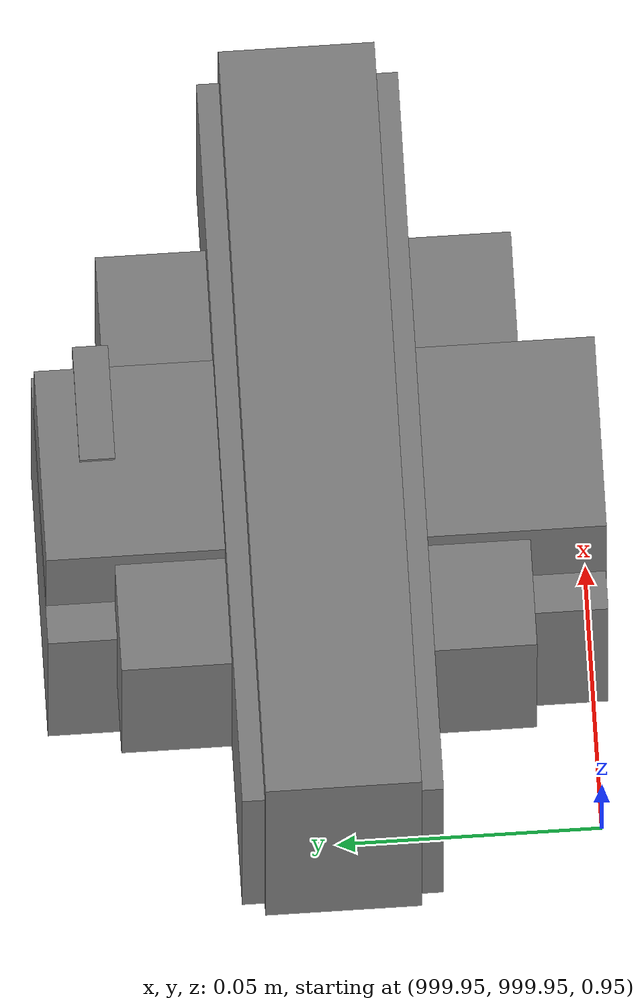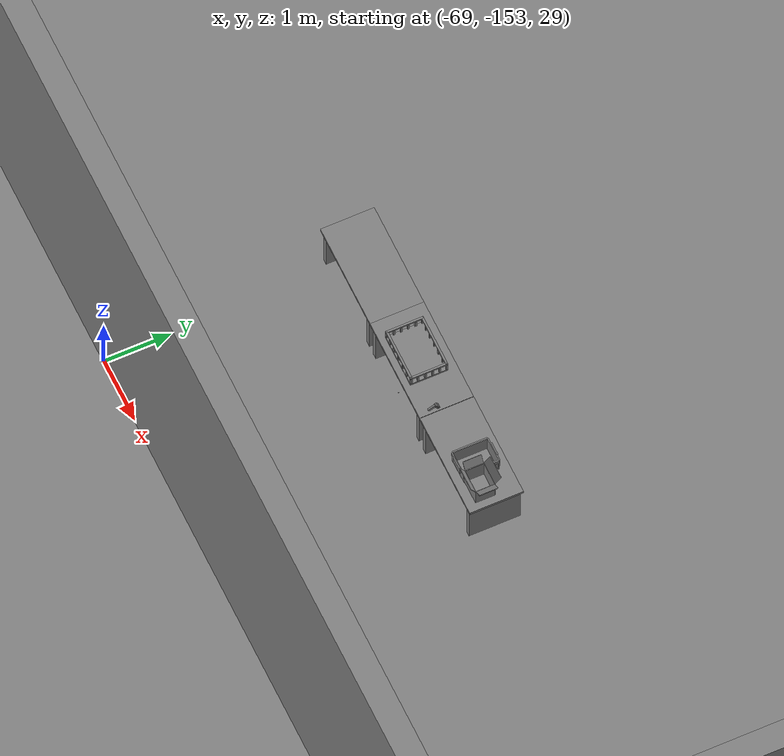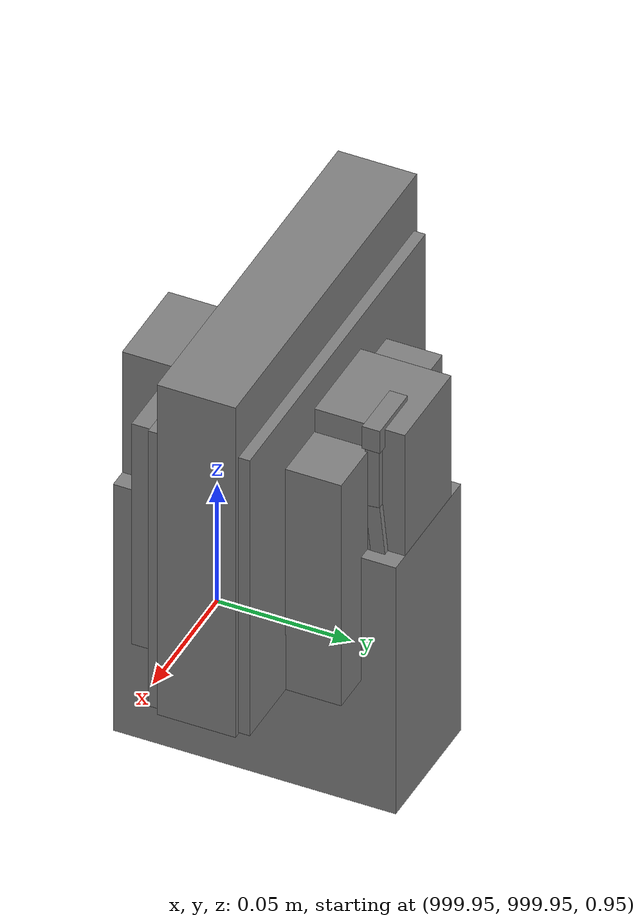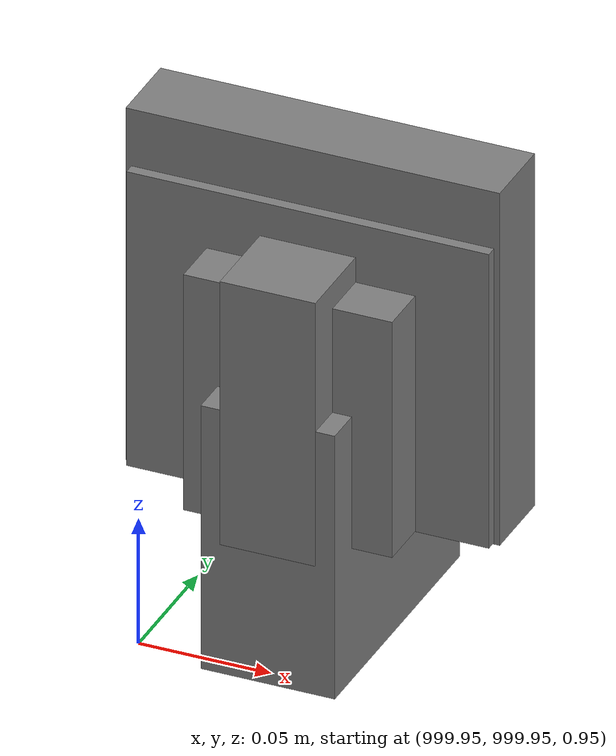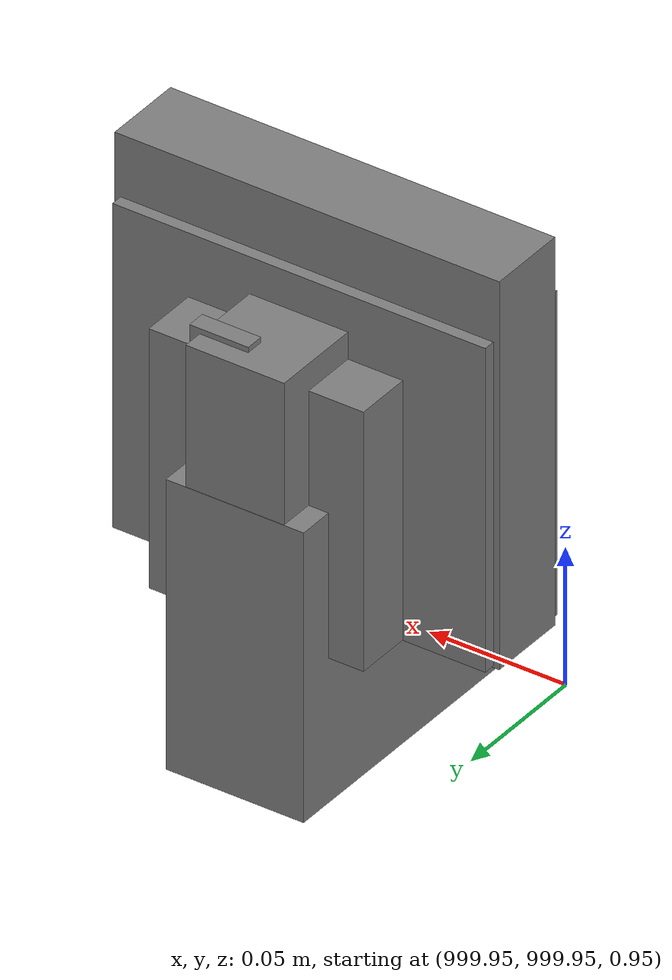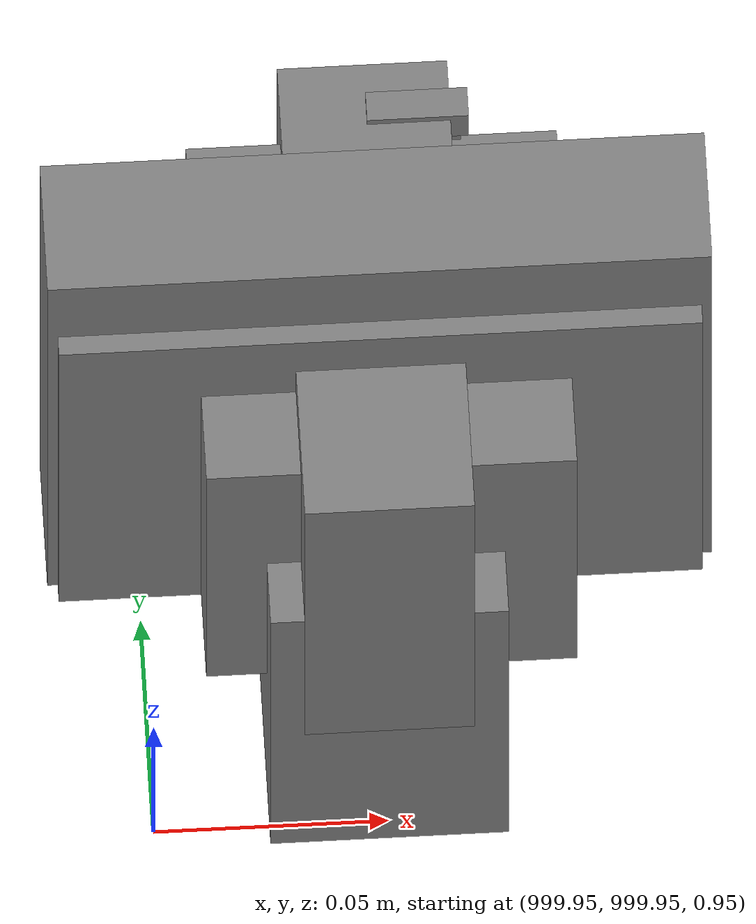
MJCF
<mujoco>
    <option gravity="0.000000000 0.000000000 -9.810000420" timestep="0.0049999999" integrator="implicitfast" density="1.225" viscosity="1.8000001e-05" noslip_iterations="10" iterations="100" sdf_iterations="50">
        <flag multiccd="disable"/>
    </option>
    <size memory="1000M"/>
    <compiler coordinate="local"/>
    <worldbody>
        <light cutoff="30" pos="0 1 1" dir="0 -1 -2"/>
        <light cutoff="30" pos="0 -1 1" dir="0 1 -2"/>
        <body pos="-64.866622925 -149.383972168 30.183746338" euler="89.999984741 89.999946594 0.000000000" name="openloong_gripper_2f85_fix_base_usda_bluebox_01">
            <geom contype="1" conaffinity="1" density="1000" type="box" material="" rgba="0.500000000 0.500000000 0.500000000 1.000000000" solimp="0.899999976 0.949999988 0.001000000" friction="1.000000000 0.005000000 0.000100000" solref="0.020000000 1.000000000" margin="0" condim="3" group="0" pos="0.276580811 0.187225342 0.000068665" quat="0.707106948 0.000077471 0.707106352 0.000077486" size="0.100000001 0.057999998 0.010000000" name="openloong_gripper_2f85_fix_base_usda_geom_14E7C6E3_F9D0_4EA9_985C_A5C26D5677F5"/>
            <geom contype="1" conaffinity="1" density="1000" type="box" material="" rgba="0.500000000 0.500000000 0.500000000 1.000000000" solimp="0.899999976 0.949999988 0.001000000" friction="1.000000000 0.005000000 0.000100000" solref="0.020000000 1.000000000" margin="0" condim="3" group="0" pos="0.000000000 0.002883911 0.000000000" quat="0.999999881 0.000000000 0.000000000 0.000000000" size="0.254000008 0.003000000 0.172000006" name="openloong_gripper_2f85_fix_base_usda_geom_36D827DF_0C59_4DA0_BF3E_A82363EF5728"/>
            <geom contype="1" conaffinity="1" density="1000" type="box" material="" rgba="0.500000000 0.500000000 0.500000000 1.000000000" solimp="0.899999976 0.949999988 0.001000000" friction="1.000000000 0.005000000 0.000100000" solref="0.020000000 1.000000000" margin="0" condim="3" group="0" pos="0.000000000 0.124874115 0.173484802" quat="0.999796331 0.020176515 -0.000000015 0.000000030" size="0.259999990 0.119999997 0.007000000" name="openloong_gripper_2f85_fix_base_usda_geom_90727F3D_9262_455D_9D5F_C4926B7CA5E6"/>
            <geom contype="1" conaffinity="1" density="1000" type="box" material="" rgba="0.500000000 0.500000000 0.500000000 1.000000000" solimp="0.899999976 0.949999988 0.001000000" friction="1.000000000 0.005000000 0.000100000" solref="0.020000000 1.000000000" margin="0" condim="3" group="0" pos="0.000000000 0.124874115 -0.173469543" quat="0.999796331 -0.020176545 -0.000000015 0.000000000" size="0.259999990 0.119999997 0.007000000" name="openloong_gripper_2f85_fix_base_usda_geom_A158D791_C219_4E01_8859_A9C1C9BFB46F"/>
            <geom contype="1" conaffinity="1" density="1000" type="box" material="" rgba="0.500000000 0.500000000 0.500000000 1.000000000" solimp="0.899999976 0.949999988 0.001000000" friction="1.000000000 0.005000000 0.000100000" solref="0.020000000 1.000000000" margin="0" condim="3" group="0" pos="0.000000000 0.214008331 0.188980103" quat="0.999912977 0.013176724 0.000000015 0.000000000" size="0.259999990 0.029999999 0.012500000" name="openloong_gripper_2f85_fix_base_usda_geom_AA34D041_9C99_4E33_9465_1AE5ABD87B30"/>
            <geom contype="1" conaffinity="1" density="1000" type="box" material="" rgba="0.500000000 0.500000000 0.500000000 1.000000000" solimp="0.899999976 0.949999988 0.001000000" friction="1.000000000 0.005000000 0.000100000" solref="0.020000000 1.000000000" margin="0" condim="3" group="0" pos="-0.258361816 0.125289917 0.001876831" quat="0.702796936 -0.020792112 0.710783124 0.020769298" size="0.189999998 0.119999997 0.009000000" name="openloong_gripper_2f85_fix_base_usda_geom_B8926B5B_693A_4122_AA56_7D79FA1C0797"/>
            <geom contype="1" conaffinity="1" density="1000" type="box" material="" rgba="0.500000000 0.500000000 0.500000000 1.000000000" solimp="0.899999976 0.949999988 0.001000000" friction="1.000000000 0.005000000 0.000100000" solref="0.020000000 1.000000000" margin="0" condim="3" group="0" pos="0.000000000 0.214008331 -0.188980103" quat="0.999912977 -0.013176769 0.000000030 0.000000015" size="0.259999990 0.029999999 0.012500000" name="openloong_gripper_2f85_fix_base_usda_geom_F90732B3_FBA2_4752_B5A5_9DB7E9DC659F"/>
            <geom contype="1" conaffinity="1" density="1000" type="box" material="" rgba="0.500000000 0.500000000 0.500000000 1.000000000" solimp="0.899999976 0.949999988 0.001000000" friction="1.000000000 0.005000000 0.000100000" solref="0.020000000 1.000000000" margin="0" condim="3" group="0" pos="-0.276611328 0.187225342 0.000068665" quat="0.707106650 0.000077441 0.707106709 0.000077456" size="0.100000001 0.057999998 0.010000000" name="openloong_gripper_2f85_fix_base_usda_geom_BD482DCC_8A01_481E_B43F_01972263B010"/>
            <geom contype="1" conaffinity="1" density="1000" type="box" material="" rgba="0.500000000 0.500000000 0.500000000 1.000000000" solimp="0.899999976 0.949999988 0.001000000" friction="1.000000000 0.005000000 0.000100000" solref="0.020000000 1.000000000" margin="0" condim="3" group="0" pos="0.258331299 0.125289917 0.001876831" quat="0.702851415 0.018856421 0.710823774 -0.019329369" size="0.189999998 0.119999997 0.009000000" name="openloong_gripper_2f85_fix_base_usda_geom_7C1439A9_691E_41CD_B5E8_4EEFEF976387"/>
            <freejoint name="openloong_gripper_2f85_fix_base_usda_bluebox_01_joint"/>
            <site size="0.005000000 0.005000000 0.005000000" rgba="0.500000000 0.500000000 0.500000000 1.000000000" pos="0.000000000 0.000000000 0.000000000" quat="0.999961913 0.008726534 0.000000000 0.000000000" group="0" type="sphere" name="openloong_gripper_2f85_fix_base_usda_bluebox_01site"/>
        </body>
        <body pos="-64.496299744 -149.491867065 30.235729218" euler="0.000000000 0.000000000 89.999946594" name="openloong_gripper_2f85_fix_base_usda_cardboardbox_01">
            <geom contype="1" conaffinity="1" density="1000" type="box" material="" rgba="0.500000000 0.500000000 0.500000000 1.000000000" solimp="0.899999976 0.949999988 0.001000000" friction="1.000000000 0.005000000 0.000100000" solref="0.020000000 1.000000000" margin="0" condim="3" group="0" pos="-0.003166199 -0.004086494 0.005052090" quat="1.000000000 0.000000000 0.000000000 0.000000000" size="0.142499998 0.177500010 0.005000000" name="openloong_gripper_2f85_fix_base_usda_geom_182F6991_182F_49B8_8FEF_DEC2CCAC1829"/>
            <geom contype="1" conaffinity="1" density="1000" type="box" material="" rgba="0.500000000 0.500000000 0.500000000 1.000000000" solimp="0.899999976 0.949999988 0.001000000" friction="1.000000000 0.005000000 0.000100000" solref="0.020000000 1.000000000" margin="0" condim="3" group="0" pos="-0.003166199 0.170316696 0.150570869" quat="1.000000000 0.000000000 0.000000000 0.000000000" size="0.142499998 0.005000000 0.149999991" name="openloong_gripper_2f85_fix_base_usda_geom_1EA5BC84_8EBF_4562_B641_6BDE4F72F8B0"/>
            <geom contype="1" conaffinity="1" density="1000" type="box" material="" rgba="0.500000000 0.500000000 0.500000000 1.000000000" solimp="0.899999976 0.949999988 0.001000000" friction="1.000000000 0.005000000 0.000100000" solref="0.020000000 1.000000000" margin="0" condim="3" group="0" pos="-0.147399902 -0.005307198 0.150570869" quat="1.000000000 0.000000000 0.000000000 0.000000000" size="0.005000000 0.177500010 0.149999991" name="openloong_gripper_2f85_fix_base_usda_geom_4FD192BD_26A9_48A5_A546_D6C9FFE0538D"/>
            <geom contype="1" conaffinity="1" density="1000" type="box" material="" rgba="0.500000000 0.500000000 0.500000000 1.000000000" solimp="0.899999976 0.949999988 0.001000000" friction="1.000000000 0.005000000 0.000100000" solref="0.020000000 1.000000000" margin="0" condim="3" group="0" pos="0.140275955 -0.005307198 0.150570869" quat="1.000000000 0.000000000 0.000000000 0.000000000" size="0.005000000 0.177500010 0.149999991" name="openloong_gripper_2f85_fix_base_usda_geom_678211ED_28DE_4145_9D56_C09CD6690246"/>
            <geom contype="1" conaffinity="1" density="1000" type="box" material="" rgba="0.500000000 0.500000000 0.500000000 1.000000000" solimp="0.899999976 0.949999988 0.001000000" friction="1.000000000 0.005000000 0.000100000" solref="0.020000000 1.000000000" margin="0" condim="3" group="0" pos="-0.003166199 -0.181550980 0.150570869" quat="1.000000000 0.000000000 0.000000000 0.000000000" size="0.142499998 0.005000000 0.149999991" name="openloong_gripper_2f85_fix_base_usda_geom_1C342B91_BD59_400B_B832_BD7A94E0BF09"/>
            <freejoint name="openloong_gripper_2f85_fix_base_usda_cardboardbox_01_joint"/>
            <site size="0.005000000 0.005000000 0.005000000" rgba="0.500000000 0.500000000 0.500000000 1.000000000" pos="0.000000000 0.000000000 0.000000000" quat="0.999961913 0.008726535 0.000000000 0.000000000" group="0" type="sphere" name="openloong_gripper_2f85_fix_base_usda_site_8AF8831F_8633_4D01_8D07_6ABC249A584B"/>
            <body pos="0.139160156 -0.004048347 0.301930904" euler="-179.999954224 49.383502960 179.999954224" name="openloong_gripper_2f85_fix_base_usda_A1_006">
                <geom contype="1" conaffinity="1" density="1000" type="box" material="" rgba="0.500000000 0.500000000 0.500000000 1.000000000" solimp="0.899999976 0.949999988 0.001000000" friction="1.000000000 0.005000000 0.000100000" solref="0.020000000 1.000000000" margin="0" condim="3" group="0" pos="-0.071587563 0.000009537 0.001745224" quat="0.999999881 0.000000000 0.000000000 0.000000000" size="0.071249999 0.179999992 0.002500000" name="openloong_gripper_2f85_fix_base_usda_geom_24A7152E_B601_492A_9ED2_145E1A2E9C1D"/>
                <joint armature="0" stiffness="0.07" damping="0.0099999998" axis="0.000000 1.000000 0.000000" type="hinge" name="openloong_gripper_2f85_fix_base_usda_A1_006"/>
            </body>
            <body pos="-0.145902634 -0.004086494 0.301938057" euler="-180.000000000 -60.000011444 -180.000000000" name="openloong_gripper_2f85_fix_base_usda_A2_006">
                <geom contype="1" conaffinity="1" density="1000" type="box" material="" rgba="0.500000000 0.500000000 0.500000000 1.000000000" solimp="0.899999976 0.949999988 0.001000000" friction="1.000000000 0.005000000 0.000100000" solref="0.020000000 1.000000000" margin="0" condim="3" group="0" pos="0.071268082 0.000009537 0.002717972" quat="0.000002921 0.000000000 -0.000000030 0.999999881" size="0.071249999 0.179999992 0.002500000" name="openloong_gripper_2f85_fix_base_usda_geom_DBB565DF_934C_4C82_A48F_3E7E14040B86"/>
                <joint armature="0" stiffness="0.07" damping="0.0099999998" axis="0.000000 1.000000 0.000000" type="hinge" name="openloong_gripper_2f85_fix_base_usda_A2_006"/>
            </body>
            <body pos="-0.003385544 0.175991058 0.301930904" euler="-125.858116150 -0.000004561 0.000002331" name="openloong_gripper_2f85_fix_base_usda_B2_006">
                <geom contype="1" conaffinity="1" density="1000" type="box" material="" rgba="0.500000000 0.500000000 0.500000000 1.000000000" solimp="0.899999976 0.949999988 0.001000000" friction="1.000000000 0.005000000 0.000100000" solref="0.020000000 1.000000000" margin="0" condim="3" group="0" pos="0.000009537 -0.070939064 -0.002470016" quat="0.999614120 0.027776197 -0.000000015 0.000000030" size="0.137500003 0.064999998 0.005000000" name="openloong_gripper_2f85_fix_base_usda_geom_09628B21_C643_49F9_B670_2087107B3E9C"/>
                <joint armature="0" stiffness="0.07" damping="0.0099999998" axis="1.000000 0.000000 0.000000" type="hinge" name="openloong_gripper_2f85_fix_base_usda_B2_006"/>
            </body>
            <body pos="-0.003385544 -0.184140205 0.301938057" euler="147.805557251 0.000000000 0.000000000" name="openloong_gripper_2f85_fix_base_usda_B1_006">
                <geom contype="1" conaffinity="1" density="1000" type="box" material="" rgba="0.500000000 0.500000000 0.500000000 1.000000000" solimp="0.899999976 0.949999988 0.001000000" friction="1.000000000 0.005000000 0.000100000" solref="0.020000000 1.000000000" margin="0" condim="3" group="0" pos="-0.000028610 0.070202351 -0.002703667" quat="0.999614179 -0.027776167 0.000000000 0.000000000" size="0.137500003 0.064999998 0.005000000" name="openloong_gripper_2f85_fix_base_usda_geom_4237CBEB_7829_4ACF_A3CC_26319AE9157D"/>
                <joint armature="0" stiffness="0.07" damping="0.0099999998" axis="1.000000 0.000000 0.000000" type="hinge" name="openloong_gripper_2f85_fix_base_usda_B1_006"/>
            </body>
        </body>
        <body pos="-65.882858276 -149.481979370 30.229999542" euler="-64.487716675 0.000000000 0.000000000" name="openloong_gripper_2f85_fix_base_usda_Barcode">
            <geom contype="1" conaffinity="1" density="1000" type="box" material="" rgba="0.500000000 0.500000000 0.500000000 1.000000000" solimp="0.899999976 0.949999988 0.001000000" friction="1.000000000 0.005000000 0.000100000" solref="0.020000000 1.000000000" margin="0" condim="3" group="0" pos="0.000000000 0.013038635 0.001419067" quat="0.000000000 0.000000000 0.000000000 1.000000119" size="0.034000002 0.010000000 0.017999999" name="openloong_gripper_2f85_fix_base_usda_geom_464EA002_FB8F_4419_9E62_D82B47B50879"/>
            <geom contype="1" conaffinity="1" density="1000" type="box" material="" rgba="0.500000000 0.500000000 0.500000000 1.000000000" solimp="0.899999976 0.949999988 0.001000000" friction="1.000000000 0.005000000 0.000100000" solref="0.020000000 1.000000000" margin="0" condim="3" group="0" pos="0.000000000 -0.035301208 -0.007095337" quat="0.000000000 0.000000000 -0.043619365 0.999048233" size="0.028999999 0.010000000 0.020000000" name="openloong_gripper_2f85_fix_base_usda_geom_5EDFA1FA_E1B1_43C8_8091_345717442FD7"/>
            <geom contype="1" conaffinity="1" density="1000" type="box" material="" rgba="0.500000000 0.500000000 0.500000000 1.000000000" solimp="0.899999976 0.949999988 0.001000000" friction="1.000000000 0.005000000 0.000100000" solref="0.020000000 1.000000000" margin="0" condim="3" group="0" pos="0.000000000 -0.043411255 -0.011749268" quat="0.922262907 0.386563420 0.000000000 0.000000000" size="0.026000001 0.010000000 0.020000000" name="openloong_gripper_2f85_fix_base_usda_geom_8CCB2E4E_AB4D_4845_91B7_66F160F11D6F"/>
            <geom contype="1" conaffinity="1" density="1000" type="box" material="" rgba="0.500000000 0.500000000 0.500000000 1.000000000" solimp="0.899999976 0.949999988 0.001000000" friction="1.000000000 0.005000000 0.000100000" solref="0.020000000 1.000000000" margin="0" condim="3" group="0" pos="0.000000000 -0.016967773 -0.031860352" quat="0.000000000 0.000000000 0.000000000 1.000000119" size="0.008000000 0.010000000 0.013000000" name="openloong_gripper_2f85_fix_base_usda_geom_5609E5AF_B925_42BB_8CDA_531484D83161"/>
            <geom contype="1" conaffinity="1" density="1000" type="box" material="" rgba="0.500000000 0.500000000 0.500000000 1.000000000" solimp="0.899999976 0.949999988 0.001000000" friction="1.000000000 0.005000000 0.000100000" solref="0.020000000 1.000000000" margin="0" condim="3" group="0" pos="0.000000000 -0.001869202 0.000312805" quat="0.953716993 0.300705761 0.000000000 0.000000000" size="0.032000002 0.010000000 0.018999999" name="openloong_gripper_2f85_fix_base_usda_geom_B2DA0069_1AF9_434A_A249_B8C93060F17D"/>
            <geom contype="1" conaffinity="1" density="1000" type="box" material="" rgba="0.500000000 0.500000000 0.500000000 1.000000000" solimp="0.899999976 0.949999988 0.001000000" friction="1.000000000 0.005000000 0.000100000" solref="0.020000000 1.000000000" margin="0" condim="3" group="0" pos="0.000000000 -0.019531250 -0.003173828" quat="0.953716993 0.300705761 0.000000000 0.000000000" size="0.030999999 0.010000000 0.020000000" name="openloong_gripper_2f85_fix_base_usda_geom_4111454C_730A_4EA5_ADC1_E23D3722B443"/>
            <geom contype="1" conaffinity="1" density="1000" type="box" material="" rgba="0.500000000 0.500000000 0.500000000 1.000000000" solimp="0.899999976 0.949999988 0.001000000" friction="1.000000000 0.005000000 0.000100000" solref="0.020000000 1.000000000" margin="0" condim="3" group="0" pos="0.000000000 -0.035301208 -0.007095337" quat="0.953716993 0.300705761 0.000000000 0.000000000" size="0.028999999 0.010000000 0.020000000" name="openloong_gripper_2f85_fix_base_usda_geom_0AEA17F1_AB72_4686_BCE0_EC0C1F7145F0"/>
            <geom contype="1" conaffinity="1" density="1000" type="box" material="" rgba="0.500000000 0.500000000 0.500000000 1.000000000" solimp="0.899999976 0.949999988 0.001000000" friction="1.000000000 0.005000000 0.000100000" solref="0.020000000 1.000000000" margin="0" condim="3" group="0" pos="0.000000000 -0.042617798 -0.071121216" quat="0.000000000 0.000000000 0.000000000 1.000000119" size="0.013000000 0.021000000 0.059999999" name="openloong_gripper_2f85_fix_base_usda_geom_340A32CF_7202_4C49_87C0_C7B1E208A1F0"/>
            <freejoint name="openloong_gripper_2f85_fix_base_usda_Barcode_joint"/>
            <site size="0.005000000 0.005000000 0.005000000" rgba="0.500000000 0.500000000 0.500000000 1.000000000" pos="0.000000000 0.000000000 0.000000000" quat="1.000000000 0.000000000 0.000000000 0.000000000" group="0" type="sphere" name="openloong_gripper_2f85_fix_base_usda_Barcode_site"/>
        </body>
        <body pos="-66.745018005 -149.392349243 30.184000015" euler="0.000000000 0.000000000 89.999946594" name="[22332032449449]_Basket_01">
            <geom contype="1" conaffinity="1" density="1000" type="box" material="" rgba="0.500000000 0.500000000 0.500000000 1.000000000" solimp="0.899999976 0.949999988 0.001000000" friction="1.000000000 0.005000000 0.000100000" solref="0.020000000 1.000000000" margin="0" condim="3" group="0" pos="-0.052425385 0.389207840 0.089787483" quat="0.707107008 0.000000000 0.000000000 0.707106411" size="0.014249999 0.014249999 0.059999999" name="[22332032449449]_geom_DF7DC9E8_66A0_4D3B_ADEA_E6B5B5C2549A"/>
            <geom contype="1" conaffinity="1" density="1000" type="box" material="" rgba="0.500000000 0.500000000 0.500000000 1.000000000" solimp="0.899999976 0.949999988 0.001000000" friction="1.000000000 0.005000000 0.000100000" solref="0.020000000 1.000000000" margin="0" condim="3" group="0" pos="0.264015198 -0.133043289 0.089787483" quat="0.707107008 0.000000000 0.000000000 0.707106411" size="0.014249999 0.014249999 0.059999999" name="[22332032449449]_geom_D0B08B64_D5DE_4A57_83AE_2DE6E0D88A64"/>
            <geom contype="1" conaffinity="1" density="1000" type="box" material="" rgba="0.500000000 0.500000000 0.500000000 1.000000000" solimp="0.899999976 0.949999988 0.001000000" friction="1.000000000 0.005000000 0.000100000" solref="0.020000000 1.000000000" margin="0" condim="3" group="0" pos="-0.264015198 -0.265548706 0.089793205" quat="0.707107008 0.000000000 0.000000000 0.707106411" size="0.014249999 0.014249999 0.059999999" name="[22332032449449]_geom_7F9282B7_3F27_4775_92A5_B6A55F3B7ACB"/>
            <geom contype="1" conaffinity="1" density="1000" type="box" material="" rgba="0.500000000 0.500000000 0.500000000 1.000000000" solimp="0.899999976 0.949999988 0.001000000" friction="1.000000000 0.005000000 0.000100000" solref="0.020000000 1.000000000" margin="0" condim="3" group="0" pos="-0.160263062 -0.389322281 0.089793205" quat="0.707107008 0.000000000 0.000000000 0.707106411" size="0.014249999 0.014249999 0.059999999" name="[22332032449449]_geom_02363076_C120_4C5D_9922_CC5990C59553"/>
            <geom contype="1" conaffinity="1" density="1000" type="box" material="" rgba="0.500000000 0.500000000 0.500000000 1.000000000" solimp="0.899999976 0.949999988 0.001000000" friction="1.000000000 0.005000000 0.000100000" solref="0.020000000 1.000000000" margin="0" condim="3" group="0" pos="0.162265778 -0.389322281 0.089787483" quat="0.707107008 0.000000000 0.000000000 0.707106411" size="0.014249999 0.014249999 0.059999999" name="[22332032449449]_geom_FDECCE97_4F9B_49D2_AEB7_009E13F667BC"/>
            <geom contype="1" conaffinity="1" density="1000" type="box" material="" rgba="0.500000000 0.500000000 0.500000000 1.000000000" solimp="0.899999976 0.949999988 0.001000000" friction="1.000000000 0.005000000 0.000100000" solref="0.020000000 1.000000000" margin="0" condim="3" group="0" pos="0.264015198 0.389207840 0.089787483" quat="0.707107008 0.000000000 0.000000000 0.707106411" size="0.014249999 0.014249999 0.059999999" name="[22332032449449]_geom_12F2EFE3_C012_484A_90C8_7DABDBC7116F"/>
            <geom contype="1" conaffinity="1" density="1000" type="box" material="" rgba="0.500000000 0.500000000 0.500000000 1.000000000" solimp="0.899999976 0.949999988 0.001000000" friction="1.000000000 0.005000000 0.000100000" solref="0.020000000 1.000000000" margin="0" condim="3" group="0" pos="-0.264015198 -0.133043289 0.089793205" quat="0.707107008 0.000000000 0.000000000 0.707106411" size="0.014249999 0.014249999 0.059999999" name="[22332032449449]_geom_1C6C295D_28E0_459A_92E3_AFF063137B90"/>
            <geom contype="1" conaffinity="1" density="1000" type="box" material="" rgba="0.500000000 0.500000000 0.500000000 1.000000000" solimp="0.899999976 0.949999988 0.001000000" friction="1.000000000 0.005000000 0.000100000" solref="0.020000000 1.000000000" margin="0" condim="3" group="0" pos="-0.264026642 0.269256592 0.089793205" quat="0.707107008 0.000000000 0.000000000 0.707106411" size="0.014249999 0.014249999 0.059999999" name="[22332032449449]_geom_F3E223ED_ADB1_4847_95F0_EE14328F206D"/>
            <geom contype="1" conaffinity="1" density="1000" type="box" material="" rgba="0.500000000 0.500000000 0.500000000 1.000000000" solimp="0.899999976 0.949999988 0.001000000" friction="1.000000000 0.005000000 0.000100000" solref="0.020000000 1.000000000" margin="0" condim="3" group="0" pos="0.054462433 0.389207840 0.089787483" quat="0.707107008 0.000000000 0.000000000 0.707106411" size="0.014249999 0.014249999 0.059999999" name="[22332032449449]_geom_33F052FB_44B9_4613_BA86_97A15A17140B"/>
            <geom contype="1" conaffinity="1" density="1000" type="box" material="" rgba="0.500000000 0.500000000 0.500000000 1.000000000" solimp="0.899999976 0.949999988 0.001000000" friction="1.000000000 0.005000000 0.000100000" solref="0.020000000 1.000000000" margin="0" condim="3" group="0" pos="0.054462433 -0.389322281 0.089787483" quat="0.707107008 0.000000000 0.000000000 0.707106411" size="0.014249999 0.014249999 0.059999999" name="[22332032449449]_geom_A86B1E63_B416_4742_8AEB_076F4B89A01E"/>
            <geom contype="1" conaffinity="1" density="1000" type="box" material="" rgba="0.500000000 0.500000000 0.500000000 1.000000000" solimp="0.899999976 0.949999988 0.001000000" friction="1.000000000 0.005000000 0.000100000" solref="0.020000000 1.000000000" margin="0" condim="3" group="0" pos="0.264015198 0.269256592 0.089793205" quat="0.707107008 0.000000000 0.000000000 0.707106411" size="0.014249999 0.014249999 0.059999999" name="[22332032449449]_geom_AFCD389B_C504_47B8_9B50_CECAF1C4D4C2"/>
            <geom contype="1" conaffinity="1" density="1000" type="box" material="" rgba="0.500000000 0.500000000 0.500000000 1.000000000" solimp="0.899999976 0.949999988 0.001000000" friction="1.000000000 0.005000000 0.000100000" solref="0.020000000 1.000000000" margin="0" condim="3" group="0" pos="0.264015198 -0.389322281 0.089787483" quat="0.707107008 0.000000000 0.000000000 0.707106411" size="0.014249999 0.014249999 0.059999999" name="[22332032449449]_geom_0BF28285_D281_4692_B8B4_5F5F687E7F75"/>
            <geom contype="1" conaffinity="1" density="1000" type="box" material="" rgba="0.500000000 0.500000000 0.500000000 1.000000000" solimp="0.899999976 0.949999988 0.001000000" friction="1.000000000 0.005000000 0.000100000" solref="0.020000000 1.000000000" margin="0" condim="3" group="0" pos="0.000000000 0.000000000 0.015998840" quat="0.707107008 0.000000000 0.000000000 0.707106411" size="0.403499991 0.279000014 0.015750000" name="[22332032449449]_geom_51AC9FA1_E272_4DC9_B1C5_74EBD6E56674"/>
            <geom contype="1" conaffinity="1" density="1000" type="box" material="" rgba="0.500000000 0.500000000 0.500000000 1.000000000" solimp="0.899999976 0.949999988 0.001000000" friction="1.000000000 0.005000000 0.000100000" solref="0.020000000 1.000000000" margin="0" condim="3" group="0" pos="0.000000000 -0.389476776 0.163619041" quat="0.707107008 0.000000000 0.000000000 0.707106411" size="0.015000000 0.277500004 0.015750000" name="[22332032449449]_geom_DCA47F64_0DA4_42D2_9922_B1F3B28EFC20"/>
            <geom contype="1" conaffinity="1" density="1000" type="box" material="" rgba="0.500000000 0.500000000 0.500000000 1.000000000" solimp="0.899999976 0.949999988 0.001000000" friction="1.000000000 0.005000000 0.000100000" solref="0.020000000 1.000000000" margin="0" condim="3" group="0" pos="0.162265778 0.389207840 0.089787483" quat="0.707107008 0.000000000 0.000000000 0.707106411" size="0.014249999 0.014249999 0.059999999" name="[22332032449449]_geom_B069489A_F622_4C52_9860_8181DD41A4FB"/>
            <geom contype="1" conaffinity="1" density="1000" type="box" material="" rgba="0.500000000 0.500000000 0.500000000 1.000000000" solimp="0.899999976 0.949999988 0.001000000" friction="1.000000000 0.005000000 0.000100000" solref="0.020000000 1.000000000" margin="0" condim="3" group="0" pos="0.000000000 0.389471054 0.163619041" quat="0.707107008 0.000000000 0.000000000 0.707106411" size="0.015000000 0.277500004 0.015750000" name="[22332032449449]_geom_2CE13CF0_C810_45AB_A327_23CCA70238A8"/>
            <geom contype="1" conaffinity="1" density="1000" type="box" material="" rgba="0.500000000 0.500000000 0.500000000 1.000000000" solimp="0.899999976 0.949999988 0.001000000" friction="1.000000000 0.005000000 0.000100000" solref="0.020000000 1.000000000" margin="0" condim="3" group="0" pos="-0.263511658 0.000000000 0.163619041" quat="0.707107008 0.000000000 0.000000000 0.707106411" size="0.403499991 0.015000000 0.015750000" name="[22332032449449]_geom_5748CC93_4428_4DB7_81A1_A895CB9D0061"/>
            <geom contype="1" conaffinity="1" density="1000" type="box" material="" rgba="0.500000000 0.500000000 0.500000000 1.000000000" solimp="0.899999976 0.949999988 0.001000000" friction="1.000000000 0.005000000 0.000100000" solref="0.020000000 1.000000000" margin="0" condim="3" group="0" pos="-0.264015198 0.141334534 0.089793205" quat="0.707107008 0.000000000 0.000000000 0.707106411" size="0.014249999 0.014249999 0.059999999" name="[22332032449449]_geom_66FF50A5_C1F9_4892_8B42_A9A84E90D4A9"/>
            <geom contype="1" conaffinity="1" density="1000" type="box" material="" rgba="0.500000000 0.500000000 0.500000000 1.000000000" solimp="0.899999976 0.949999988 0.001000000" friction="1.000000000 0.005000000 0.000100000" solref="0.020000000 1.000000000" margin="0" condim="3" group="0" pos="0.264015198 -0.265548706 0.089787483" quat="0.707107008 0.000000000 0.000000000 0.707106411" size="0.014249999 0.014249999 0.059999999" name="[22332032449449]_geom_30B6B264_5195_4A46_B04D_0CE6D741266B"/>
            <geom contype="1" conaffinity="1" density="1000" type="box" material="" rgba="0.500000000 0.500000000 0.500000000 1.000000000" solimp="0.899999976 0.949999988 0.001000000" friction="1.000000000 0.005000000 0.000100000" solref="0.020000000 1.000000000" margin="0" condim="3" group="0" pos="-0.160263062 0.389207840 0.089787483" quat="0.707107008 0.000000000 0.000000000 0.707106411" size="0.014249999 0.014249999 0.059999999" name="[22332032449449]_geom_3250FF41_1132_4448_B9CE_25C396007BDD"/>
            <geom contype="1" conaffinity="1" density="1000" type="box" material="" rgba="0.500000000 0.500000000 0.500000000 1.000000000" solimp="0.899999976 0.949999988 0.001000000" friction="1.000000000 0.005000000 0.000100000" solref="0.020000000 1.000000000" margin="0" condim="3" group="0" pos="-0.052425385 -0.389322281 0.089787483" quat="0.707107008 0.000000000 0.000000000 0.707106411" size="0.014249999 0.014249999 0.059999999" name="[22332032449449]_geom_C5361D5E_178B_40ED_92B5_AB1CDDB01AEA"/>
            <geom contype="1" conaffinity="1" density="1000" type="box" material="" rgba="0.500000000 0.500000000 0.500000000 1.000000000" solimp="0.899999976 0.949999988 0.001000000" friction="1.000000000 0.005000000 0.000100000" solref="0.020000000 1.000000000" margin="0" condim="3" group="0" pos="-0.264026642 -0.389322281 0.089793205" quat="0.707107008 0.000000000 0.000000000 0.707106411" size="0.014249999 0.014249999 0.059999999" name="[22332032449449]_geom_74E3EB1A_1EA2_4EE1_9FF4_C25735107F27"/>
            <geom contype="1" conaffinity="1" density="1000" type="box" material="" rgba="0.500000000 0.500000000 0.500000000 1.000000000" solimp="0.899999976 0.949999988 0.001000000" friction="1.000000000 0.005000000 0.000100000" solref="0.020000000 1.000000000" margin="0" condim="3" group="0" pos="0.264015198 0.141334534 0.089787483" quat="0.707107008 0.000000000 0.000000000 0.707106411" size="0.014249999 0.014249999 0.059999999" name="[22332032449449]_geom_13A79BA6_BBD8_4D33_A154_50D7EF9F63F0"/>
            <geom contype="1" conaffinity="1" density="1000" type="box" material="" rgba="0.500000000 0.500000000 0.500000000 1.000000000" solimp="0.899999976 0.949999988 0.001000000" friction="1.000000000 0.005000000 0.000100000" solref="0.020000000 1.000000000" margin="0" condim="3" group="0" pos="-0.264015198 0.389207840 0.089793205" quat="0.707107008 0.000000000 0.000000000 0.707106411" size="0.014249999 0.014249999 0.059999999" name="[22332032449449]_geom_F3ADB28B_1798_4E2F_9DC1_60733C3C8B4D"/>
            <geom contype="1" conaffinity="1" density="1000" type="box" material="" rgba="0.500000000 0.500000000 0.500000000 1.000000000" solimp="0.899999976 0.949999988 0.001000000" friction="1.000000000 0.005000000 0.000100000" solref="0.020000000 1.000000000" margin="0" condim="3" group="0" pos="0.264015198 0.004480362 0.089787483" quat="0.707107008 0.000000000 0.000000000 0.707106411" size="0.014249999 0.014249999 0.059999999" name="[22332032449449]_geom_6626EBCB_4982_41D0_9455_4004526DB3AD"/>
            <geom contype="1" conaffinity="1" density="1000" type="box" material="" rgba="0.500000000 0.500000000 0.500000000 1.000000000" solimp="0.899999976 0.949999988 0.001000000" friction="1.000000000 0.005000000 0.000100000" solref="0.020000000 1.000000000" margin="0" condim="3" group="0" pos="0.263694763 -0.000011444 0.163619041" quat="0.707107008 0.000000000 0.000000000 0.707106411" size="0.403499991 0.015000000 0.015750000" name="[22332032449449]_geom_EB58FEAF_8FFD_487A_9F01_9F0EBB896819"/>
            <geom contype="1" conaffinity="1" density="1000" type="box" material="" rgba="0.500000000 0.500000000 0.500000000 1.000000000" solimp="0.899999976 0.949999988 0.001000000" friction="1.000000000 0.005000000 0.000100000" solref="0.020000000 1.000000000" margin="0" condim="3" group="0" pos="-0.264015198 0.004480362 0.089793205" quat="0.707107008 0.000000000 0.000000000 0.707106411" size="0.014249999 0.014249999 0.059999999" name="[22332032449449]_geom_F913B243_3F4B_4FA7_B360_34C9F72B87F9"/>
            <freejoint name="[22332032449449]_joint_FA730E66_42B6_4FA9_8D30_01EBA20A1809"/>
        </body>
        <body pos="0.000000000 0.000000000 0.000000000" euler="0.000000000 0.000000000 0.000000000" name="Static Objects_Static Objects">
            <geom contype="1" conaffinity="1" density="1000" type="box" material="" rgba="0.500000000 0.500000000 0.500000000 1.000000000" solimp="0.899999976 0.949999988 0.001000000" friction="1.000000000 0.005000000 0.000100000" solref="0.020000000 1.000000000" margin="0" condim="3" group="0" pos="-67.544113159 -149.365814209 29.727830887" quat="0.500000417 0.499999970 0.499999553 0.499999970" size="0.381000012 0.319999993 0.041000001" name="Static Objects_geom_6727C72B_DF45_4F15_8ED0_16E185B1F334"/>
            <geom contype="1" conaffinity="1" density="1000" type="box" material="" rgba="0.500000000 0.500000000 0.500000000 1.000000000" solimp="0.899999976 0.949999988 0.001000000" friction="1.000000000 0.005000000 0.000100000" solref="0.020000000 1.000000000" margin="0" condim="3" group="0" pos="-68.239501953 -149.365814209 30.086868286" quat="0.500000417 0.499999970 0.499999553 0.499999970" size="0.370999992 0.039500002 0.745000005" name="Static Objects_geom_B1650452_BA4D_4DA9_A5B1_217E557D63B8"/>
            <geom contype="1" conaffinity="1" density="1000" type="box" material="" rgba="0.500000000 0.500000000 0.500000000 1.000000000" solimp="0.899999976 0.949999988 0.001000000" friction="1.000000000 0.005000000 0.000100000" solref="0.020000000 1.000000000" margin="0" condim="3" group="0" pos="-68.239501953 -149.365814209 30.147235870" quat="0.500000417 0.499999970 0.499999553 0.499999970" size="0.400000006 0.022000000 0.800000012" name="Static Objects_geom_4D8FD158_D685_4F2E_8E9C_A8AC6876E1EF"/>
            <geom contype="1" conaffinity="1" density="1000" type="box" material="" rgba="0.500000000 0.500000000 0.500000000 1.000000000" solimp="0.899999976 0.949999988 0.001000000" friction="1.000000000 0.005000000 0.000100000" solref="0.020000000 1.000000000" margin="0" condim="3" group="0" pos="-68.934890747 -149.365814209 29.727830887" quat="0.500000417 0.499999970 0.499999553 0.499999970" size="0.381000012 0.319999993 0.041000001" name="Static Objects_geom_46B8769C_54AC_46B2_B22B_8C4907D234F1"/>
            <geom contype="1" conaffinity="1" density="1000" type="box" material="" rgba="0.500000000 0.500000000 0.500000000 1.000000000" solimp="0.899999976 0.949999988 0.001000000" friction="1.000000000 0.005000000 0.000100000" solref="0.020000000 1.000000000" margin="0" condim="3" group="0" pos="-68.239501953 -149.365814209 29.561563492" quat="0.500000417 0.499999970 0.499999553 0.499999970" size="0.020000000 0.022000000 0.660000026" name="Static Objects_geom_79A387CA_3B06_4BD2_A0F0_9899754FC8DB"/>
            <geom contype="1" conaffinity="1" density="1000" type="box" material="" rgba="0.500000000 0.500000000 0.500000000 1.000000000" solimp="0.899999976 0.949999988 0.001000000" friction="1.000000000 0.005000000 0.000100000" solref="0.020000000 1.000000000" margin="0" condim="3" group="0" pos="-65.945671082 -149.365814209 29.727830887" quat="0.500000417 0.499999970 0.499999553 0.499999970" size="0.381000012 0.319999993 0.041000001" name="Static Objects_geom_D547BE56_9F01_4C0E_8A9D_773C1EBB1D07"/>
            <geom contype="1" conaffinity="1" density="1000" type="box" material="" rgba="0.500000000 0.500000000 0.500000000 1.000000000" solimp="0.899999976 0.949999988 0.001000000" friction="1.000000000 0.005000000 0.000100000" solref="0.020000000 1.000000000" margin="0" condim="3" group="0" pos="-66.641059875 -149.365814209 30.086868286" quat="0.500000417 0.499999970 0.499999553 0.499999970" size="0.370999992 0.039500002 0.745000005" name="Static Objects_geom_B8680775_F906_43AE_ABD0_394B3F2C52E6"/>
            <geom contype="1" conaffinity="1" density="1000" type="box" material="" rgba="0.500000000 0.500000000 0.500000000 1.000000000" solimp="0.899999976 0.949999988 0.001000000" friction="1.000000000 0.005000000 0.000100000" solref="0.020000000 1.000000000" margin="0" condim="3" group="0" pos="-66.641059875 -149.365814209 30.147235870" quat="0.500000417 0.499999970 0.499999553 0.499999970" size="0.400000006 0.022000000 0.800000012" name="Static Objects_geom_7A38E551_4A80_47B4_8024_FE997316439D"/>
            <geom contype="1" conaffinity="1" density="1000" type="box" material="" rgba="0.500000000 0.500000000 0.500000000 1.000000000" solimp="0.899999976 0.949999988 0.001000000" friction="1.000000000 0.005000000 0.000100000" solref="0.020000000 1.000000000" margin="0" condim="3" group="0" pos="-67.336448669 -149.365814209 29.727830887" quat="0.500000417 0.499999970 0.499999553 0.499999970" size="0.381000012 0.319999993 0.041000001" name="Static Objects_geom_D9057F56_54FF_4376_BDBE_25CFEC19A176"/>
            <geom contype="1" conaffinity="1" density="1000" type="box" material="" rgba="0.500000000 0.500000000 0.500000000 1.000000000" solimp="0.899999976 0.949999988 0.001000000" friction="1.000000000 0.005000000 0.000100000" solref="0.020000000 1.000000000" margin="0" condim="3" group="0" pos="-66.641059875 -149.365814209 29.561563492" quat="0.500000417 0.499999970 0.499999553 0.499999970" size="0.020000000 0.022000000 0.660000026" name="Static Objects_geom_E9A90B4C_0DE9_4CAD_903F_656F982F2E52"/>
            <geom contype="1" conaffinity="1" density="1000" type="box" material="" rgba="0.500000000 0.500000000 0.500000000 1.000000000" solimp="0.899999976 0.949999988 0.001000000" friction="1.000000000 0.005000000 0.000100000" solref="0.020000000 1.000000000" margin="0" condim="3" group="0" pos="-64.338577271 -149.365814209 29.727830887" quat="0.500000417 0.499999970 0.499999553 0.499999970" size="0.381000012 0.319999993 0.041000001" name="Static Objects_geom_82C10D02_B392_4A8B_A05D_3B6215516BA8"/>
            <geom contype="1" conaffinity="1" density="1000" type="box" material="" rgba="0.500000000 0.500000000 0.500000000 1.000000000" solimp="0.899999976 0.949999988 0.001000000" friction="1.000000000 0.005000000 0.000100000" solref="0.020000000 1.000000000" margin="0" condim="3" group="0" pos="-65.033966064 -149.365814209 30.086868286" quat="0.500000417 0.499999970 0.499999553 0.499999970" size="0.370999992 0.039500002 0.745000005" name="Static Objects_geom_5BD33C6A_7A0C_494F_A455_46966572AB63"/>
            <geom contype="1" conaffinity="1" density="1000" type="box" material="" rgba="0.500000000 0.500000000 0.500000000 1.000000000" solimp="0.899999976 0.949999988 0.001000000" friction="1.000000000 0.005000000 0.000100000" solref="0.020000000 1.000000000" margin="0" condim="3" group="0" pos="-65.033966064 -149.365814209 30.147235870" quat="0.500000417 0.499999970 0.499999553 0.499999970" size="0.400000006 0.022000000 0.800000012" name="Static Objects_geom_FFC3E44F_CEBC_4E05_9401_87034CB0722E"/>
            <geom contype="1" conaffinity="1" density="1000" type="box" material="" rgba="0.500000000 0.500000000 0.500000000 1.000000000" solimp="0.899999976 0.949999988 0.001000000" friction="1.000000000 0.005000000 0.000100000" solref="0.020000000 1.000000000" margin="0" condim="3" group="0" pos="-65.729354858 -149.365814209 29.727830887" quat="0.500000417 0.499999970 0.499999553 0.499999970" size="0.381000012 0.319999993 0.041000001" name="Static Objects_geom_964E572D_DC5D_4112_99C6_6E26829F25D4"/>
            <geom contype="1" conaffinity="1" density="1000" type="box" material="" rgba="0.500000000 0.500000000 0.500000000 1.000000000" solimp="0.899999976 0.949999988 0.001000000" friction="1.000000000 0.005000000 0.000100000" solref="0.020000000 1.000000000" margin="0" condim="3" group="0" pos="-65.033966064 -149.365814209 29.561563492" quat="0.500000417 0.499999970 0.499999553 0.499999970" size="0.020000000 0.022000000 0.660000026" name="Static Objects_geom_C26CC9C8_2B7B_469C_BE4A_286829F95ED2"/>
            <geom contype="1" conaffinity="1" density="1000" type="box" material="" rgba="0.500000000 0.500000000 0.500000000 1.000000000" solimp="0.899999976 0.949999988 0.001000000" friction="1.000000000 0.005000000 0.000100000" solref="0.020000000 1.000000000" margin="0" condim="3" group="0" pos="-61.754566193 -137.853729248 33.906845093" quat="0.707107067 0.000000000 0.000000000 0.707106471" size="0.759999990 0.759999990 4.500000000" name="Static Objects_geom_66AA5B48_F07E_48DB_B242_0FDB649A241B"/>
            <geom contype="1" conaffinity="1" density="1000" type="box" material="" rgba="0.500000000 0.500000000 0.500000000 1.000000000" solimp="0.899999976 0.949999988 0.001000000" friction="1.000000000 0.005000000 0.000100000" solref="0.020000000 1.000000000" margin="0" condim="3" group="0" pos="-57.511135101 -144.927108765 31.707921982" quat="1.000000000 0.000000000 0.000000000 0.000000000" size="0.200000003 8.000000000 2.299999952" name="Static Objects_geom_B5548172_C6A0_4B65_9700_C0DD46F9360B"/>
            <geom contype="1" conaffinity="1" density="1000" type="box" material="" rgba="0.500000000 0.500000000 0.500000000 1.000000000" solimp="0.899999976 0.949999988 0.001000000" friction="1.000000000 0.005000000 0.000100000" solref="0.020000000 1.000000000" margin="0" condim="3" group="0" pos="-80.517646790 -157.574050903 31.688196182" quat="0.707107067 0.000000000 0.000000000 0.707106471" size="0.600000024 0.600000024 2.299999952" name="Static Objects_geom_B59E496B_5D39_4591_AD6B_1C97ED2D36D8"/>
            <geom contype="1" conaffinity="1" density="1000" type="box" material="" rgba="0.500000000 0.500000000 0.500000000 1.000000000" solimp="0.899999976 0.949999988 0.001000000" friction="1.000000000 0.005000000 0.000100000" solref="0.020000000 1.000000000" margin="0" condim="3" group="0" pos="-80.711044312 -147.414932251 31.666158676" quat="1.000000000 0.000000000 0.000000000 0.000000000" size="0.200000003 10.000000000 2.299999952" name="Static Objects_geom_4F0F4143_4077_4BE5_A24F_93C1BE7718BF"/>
            <geom contype="1" conaffinity="1" density="1000" type="box" material="" rgba="0.500000000 0.500000000 0.500000000 1.000000000" solimp="0.899999976 0.949999988 0.001000000" friction="1.000000000 0.005000000 0.000100000" solref="0.020000000 1.000000000" margin="0" condim="3" group="0" pos="-57.687217712 -137.434692383 31.688196182" quat="0.707107067 0.000000000 0.000000000 0.707106471" size="0.600000024 0.600000024 2.299999952" name="Static Objects_geom_230E26C7_48E7_48A1_93CA_62BD59DDA452"/>
            <geom contype="1" conaffinity="1" density="1000" type="box" material="" rgba="0.500000000 0.500000000 0.500000000 1.000000000" solimp="0.899999976 0.949999988 0.001000000" friction="1.000000000 0.005000000 0.000100000" solref="0.020000000 1.000000000" margin="0" condim="3" group="0" pos="-69.537033081 -140.263229370 31.714921951" quat="0.707107067 0.000000000 0.000000000 0.707106471" size="0.759999990 4.500000000 2.299999952" name="Static Objects_geom_41C07B97_960A_4544_9B46_9FC1684DC23C"/>
            <geom contype="1" conaffinity="1" density="1000" type="box" material="" rgba="0.500000000 0.500000000 0.500000000 1.000000000" solimp="0.899999976 0.949999988 0.001000000" friction="1.000000000 0.005000000 0.000100000" solref="0.020000000 1.000000000" margin="0" condim="3" group="0" pos="-80.073638916 -137.853713989 33.906845093" quat="0.707107067 0.000000000 0.000000000 0.707106471" size="0.759999990 0.759999990 4.500000000" name="Static Objects_geom_DF1CD797_AFCE_4D51_922D_475D0637863D"/>
            <geom contype="1" conaffinity="1" density="1000" type="box" material="" rgba="0.500000000 0.500000000 0.500000000 1.000000000" solimp="0.899999976 0.949999988 0.001000000" friction="1.000000000 0.005000000 0.000100000" solref="0.020000000 1.000000000" margin="0" condim="3" group="0" pos="-73.406707764 -155.734664917 31.707921982" quat="1.000000000 0.000000000 0.000000000 0.000000000" size="0.200000003 3.000000000 2.299999952" name="Static Objects_geom_E5525015_D444_420D_8627_0A6F7C3F9894"/>
            <geom contype="1" conaffinity="1" density="1000" type="box" material="" rgba="0.500000000 0.500000000 0.500000000 1.000000000" solimp="0.899999976 0.949999988 0.001000000" friction="1.000000000 0.005000000 0.000100000" solref="0.020000000 1.000000000" margin="0" condim="3" group="0" pos="-68.497543335 -137.448257446 31.707921982" quat="0.707107067 0.000000000 0.000000000 0.707106471" size="0.200000003 14.000000000 2.299999952" name="Static Objects_geom_14AC46AF_4CF4_458F_818F_7C3895BEA797"/>
            <geom contype="1" conaffinity="1" density="1000" type="cylinder" material="" rgba="0.500000000 0.500000000 0.500000000 1.000000000" solimp="0.899999976 0.949999988 0.001000000" friction="1.000000000 0.005000000 0.000100000" solref="0.020000000 1.000000000" margin="0" condim="3" group="0" pos="-68.868522644 -142.134506226 31.711090088" quat="0.707107067 0.000000000 0.000000000 0.707106471" size="0.509999990 2.299999952 1.000000000" name="Static Objects_geom_7391BD17_8B16_4D5B_B24B_244BB39DEDF1"/>
            <geom contype="1" conaffinity="1" density="1000" type="plane" material="" rgba="0.500000000 0.500000000 0.500000000 1.000000000" solimp="0.899999976 0.949999988 0.001000000" friction="1.000000000 0.005000000 0.000100000" solref="0.020000000 1.000000000" margin="0" condim="3" group="0" pos="-72.873703003 -147.131927490 29.409669876" quat="1.000000000 0.000000000 0.000000000 0.000000000" size="18.000000000 14.000000000 1.000000000" name="Static Objects_geom_8EE3D6B6_F9E3_423C_BFE9_45D18100C76C"/>
            <geom contype="1" conaffinity="1" density="1000" type="box" material="" rgba="0.500000000 0.500000000 0.500000000 1.000000000" solimp="0.899999976 0.949999988 0.001000000" friction="1.000000000 0.005000000 0.000100000" solref="0.020000000 1.000000000" margin="0" condim="3" group="0" pos="-79.943580627 -157.782272339 31.707921982" quat="0.707107067 0.000000000 0.000000000 0.707106471" size="0.200000003 7.000000000 2.299999952" name="Static Objects_geom_C34E5D2E_97AB_455E_B1A7_ACB621C87329"/>
            <geom contype="1" conaffinity="1" density="1000" type="box" material="" rgba="0.500000000 0.500000000 0.500000000 1.000000000" solimp="0.899999976 0.949999988 0.001000000" friction="1.000000000 0.005000000 0.000100000" solref="0.020000000 1.000000000" margin="0" condim="3" group="0" pos="-65.421028137 -152.903442383 31.707921982" quat="0.707107067 0.000000000 0.000000000 0.707106471" size="0.200000003 7.800000191 2.299999952" name="Static Objects_geom_9DF52535_2A45_4A3A_9474_A1696912A969"/>
            <geom contype="1" conaffinity="1" density="1000" type="box" material="" rgba="0.500000000 0.500000000 0.500000000 1.000000000" solimp="0.899999976 0.949999988 0.001000000" friction="1.000000000 0.005000000 0.000100000" solref="0.020000000 1.000000000" margin="0" condim="3" group="0" pos="-74.776908875 -149.964416504 31.688196182" quat="1.000000000 0.000000000 0.000000000 0.000000000" size="0.600000024 0.409999996 2.299999952" name="Static Objects_geom_E1AF02EA_5A3A_4EC9_87AB_C3E6F7EAAE1D"/>
            <geom contype="1" conaffinity="1" density="1000" type="cylinder" material="" rgba="0.500000000 0.500000000 0.500000000 1.000000000" solimp="0.899999976 0.949999988 0.001000000" friction="1.000000000 0.005000000 0.000100000" solref="0.020000000 1.000000000" margin="0" condim="3" group="0" pos="-60.161884308 -142.134506226 31.711090088" quat="0.707107067 0.000000000 0.000000000 0.707106471" size="0.509999990 2.299999952 1.000000000" name="Static Objects_geom_E24AD308_3286_4817_BCDB_CF5228F369B3"/>
            <geom contype="1" conaffinity="1" density="1000" type="cylinder" material="" rgba="0.500000000 0.500000000 0.500000000 1.000000000" solimp="0.899999976 0.949999988 0.001000000" friction="1.000000000 0.005000000 0.000100000" solref="0.020000000 1.000000000" margin="0" condim="3" group="0" pos="-75.382453918 -149.963455200 31.711090088" quat="0.707107067 0.000000000 0.000000000 0.707106471" size="0.409999996 2.299999952 1.000000000" name="Static Objects_geom_1D7BF501_F410_49D8_B672_50C998996DD6"/>
            <geom contype="1" conaffinity="1" density="1000" type="cylinder" material="" rgba="0.500000000 0.500000000 0.500000000 1.000000000" solimp="0.899999976 0.949999988 0.001000000" friction="1.000000000 0.005000000 0.000100000" solref="0.020000000 1.000000000" margin="0" condim="3" group="0" pos="-74.154960632 -149.963455200 31.711090088" quat="0.707107067 0.000000000 0.000000000 0.707106471" size="0.409999996 2.299999952 1.000000000" name="Static Objects_geom_CB78A5A4_90A0_491C_9612_9F3839D3E974"/>
            <geom contype="1" conaffinity="1" density="1000" type="cylinder" material="" rgba="0.500000000 0.500000000 0.500000000 1.000000000" solimp="0.899999976 0.949999988 0.001000000" friction="1.000000000 0.005000000 0.000100000" solref="0.020000000 1.000000000" margin="0" condim="3" group="0" pos="-77.566612244 -142.134506226 31.711090088" quat="0.707107067 0.000000000 0.000000000 0.707106471" size="0.509999990 2.299999952 1.000000000" name="Static Objects_geom_472CA6D7_BD2A_47F4_B9D9_B22D1D06FC4A"/>
        </body>
        <body pos="1000.000000000 1000.000000000 1.000000000" euler="0.000000000 0.000000000 180.000000000" name="openloong_gripper_2f85_fix_base_usda_battery_01">
            <geom contype="1" conaffinity="1" density="1000" type="box" material="" rgba="0.500000000 0.500000000 0.500000000 1.000000000" solimp="0.899999976 0.949999988 0.001000000" friction="1.000000000 0.005000000 0.000100000" solref="0.020000000 1.000000000" margin="0" condim="3" group="0" pos="-0.011123657 -0.041940309 0.101691343" quat="1.000000000 0.000000000 0.000000000 0.000000000" size="0.010800000 0.003375000 0.004725000" name="openloong_gripper_2f85_fix_base_usda_geom_A1FDF65C_9C92_4A19_AF01_F87F9B3F61C5"/>
            <geom contype="1" conaffinity="1" density="1000" type="box" material="" rgba="0.500000000 0.500000000 0.500000000 1.000000000" solimp="0.899999976 0.949999988 0.001000000" friction="1.000000000 0.005000000 0.000100000" solref="0.020000000 1.000000000" margin="0" condim="3" group="0" pos="-0.010876465 -0.044247437 0.047066893" quat="0.998702705 -0.050920475 0.000000000 0.000000000" size="0.009450001 0.002700000 0.024975000" name="openloong_gripper_2f85_fix_base_usda_geom_09D8252B_EF78_4613_8B9D_DD4A80FD8723"/>
            <geom contype="1" conaffinity="1" density="1000" type="box" material="" rgba="0.500000000 0.500000000 0.500000000 1.000000000" solimp="0.899999976 0.949999988 0.001000000" friction="1.000000000 0.005000000 0.000100000" solref="0.020000000 1.000000000" margin="0" condim="3" group="0" pos="-0.001235962 -0.000659180 0.047381196" quat="1.000000000 0.000000000 0.000000000 0.000000000" size="0.039420001 0.039150000 0.047250003" name="openloong_gripper_2f85_fix_base_usda_geom_9D74C002_4475_43A8_95D8_E60BD9E199F0"/>
            <geom contype="1" conaffinity="1" density="1000" type="box" material="" rgba="0.500000000 0.500000000 0.500000000 1.000000000" solimp="0.899999976 0.949999988 0.001000000" friction="1.000000000 0.005000000 0.000100000" solref="0.020000000 1.000000000" margin="0" condim="3" group="0" pos="-0.010876465 -0.039138794 0.009851727" quat="1.000000000 0.000000000 0.000000000 0.000000000" size="0.009450001 0.010800000 0.013500000" name="openloong_gripper_2f85_fix_base_usda_geom_708790D7_4CBD_48CF_A82E_B70044C658BF"/>
            <geom contype="1" conaffinity="1" density="1000" type="box" material="" rgba="0.500000000 0.500000000 0.500000000 1.000000000" solimp="0.899999976 0.949999988 0.001000000" friction="1.000000000 0.005000000 0.000100000" solref="0.020000000 1.000000000" margin="0" condim="3" group="0" pos="-0.010876465 -0.041528322 0.071508206" quat="1.000000000 0.000000000 0.000000000 0.000000000" size="0.009450001 0.002700000 0.027000001" name="openloong_gripper_2f85_fix_base_usda_geom_5994837B_B48C_446B_92A8_EED1CE43EEF8"/>
            <freejoint name="openloong_gripper_2f85_fix_base_usda_battery_01_joint"/>
            <site size="0.005000000 0.005000000 0.005000000" rgba="0.500000000 0.500000000 0.500000000 1.000000000" pos="0.000000000 0.000000000 0.000000000" quat="0.999961913 0.008726500 0.000000000 0.000000000" group="0" type="sphere" name="openloong_gripper_2f85_fix_base_usda_battery_01site"/>
        </body>
        <body pos="1000.000000000 1000.000000000 1.000000000" euler="0.000000000 0.000000000 180.000000000" name="openloong_gripper_2f85_fix_base_usda_wifi_box">
            <geom contype="1" conaffinity="1" density="1000" type="box" material="" rgba="0.500000000 0.500000000 0.500000000 1.000000000" solimp="0.899999976 0.949999988 0.001000000" friction="1.000000000 0.005000000 0.000100000" solref="0.020000000 1.000000000" margin="0" condim="3" group="0" pos="0.000000000 0.000000000 0.058978677" quat="0.000000000 0.000000047 0.000000000 1.000000000" size="0.068499997 0.018999999 0.059000000" name="openloong_gripper_2f85_fix_base_usda_geom_68665B47_1A73_4432_AABD_4634BE3B7BF8"/>
            <freejoint name="openloong_gripper_2f85_fix_base_usda_wifi_box_joint"/>
            <site size="0.005000000 0.005000000 0.005000000" rgba="0.500000000 0.500000000 0.500000000 1.000000000" pos="0.000000000 0.000000000 0.000000000" quat="0.999961913 0.008726500 0.000000000 0.000000000" group="0" type="sphere" name="openloong_gripper_2f85_fix_base_usda_wifi_boxsite"/>
        </body>
        <body pos="-66.361305237 -148.839309692 31.166790009" euler="-90.599319458 13.926875114 -22.514062881" mocap="true" name="spotlight4_SpotLight"/>
        <body pos="1000.000000000 1000.000000000 1.000000000" euler="0.000000000 0.000000000 180.000000000" name="openloong_gripper_2f85_fix_base_usda_cpu_fan">
            <geom contype="1" conaffinity="1" density="1000" type="box" material="" rgba="0.500000000 0.500000000 0.500000000 1.000000000" solimp="0.899999976 0.949999988 0.001000000" friction="1.000000000 0.005000000 0.000100000" solref="0.020000000 1.000000000" margin="0" condim="3" group="0" pos="0.000000000 0.000000000 0.070034981" quat="0.000000000 0.000000000 0.000000000 1.000000000" size="0.070700005 0.014699999 0.070700005" name="openloong_gripper_2f85_fix_base_usda_geom_4E43B208_C688_4611_830C_2FF5A16F78C7"/>
            <freejoint name="openloong_gripper_2f85_fix_base_usda_cpu_fan_joint"/>
            <site size="0.005000000 0.005000000 0.005000000" rgba="0.500000000 0.500000000 0.500000000 1.000000000" pos="0.000000000 0.000000000 0.000000000" quat="0.999961913 0.008726535 0.000000000 0.000000000" group="0" type="sphere" name="openloong_gripper_2f85_fix_base_usda_cpu_fancsite"/>
        </body>
        <body pos="-66.045967102 -149.379028320 31.163602829" euler="-38.340965271 -11.761636734 -143.102142334" mocap="true" name="spotlight6_SpotLight"/>
        <body pos="1000.000000000 1000.000000000 1.000000000" euler="0.000011953 0.000005123 -179.999984741" name="openloong_gripper_2f85_fix_base_usda_intel_box">
            <geom contype="1" conaffinity="1" density="1000" type="box" material="" rgba="0.500000000 0.500000000 0.500000000 1.000000000" solimp="0.899999976 0.949999988 0.001000000" friction="1.000000000 0.005000000 0.000100000" solref="0.020000000 1.000000000" margin="0" condim="3" group="0" pos="0.000000000 -0.000067139 0.000082284" quat="0.707106709 0.000000225 0.000000253 0.707106650" size="0.052800003 0.025300000 0.052800003" name="openloong_gripper_2f85_fix_base_usda_geom_F644DC11_D8F1_4610_96A8_05403ACC79FF"/>
            <freejoint name="openloong_gripper_2f85_fix_base_usda_intel_box_joint"/>
            <site size="0.005000000 0.005000000 0.005000000" rgba="0.500000000 0.500000000 0.500000000 1.000000000" pos="0.000000000 0.000000000 0.000000000" quat="0.999961913 0.008726500 0.000000000 0.000000000" group="0" type="sphere" name="openloong_gripper_2f85_fix_base_usda_intel_boxsite"/>
        </body>
        <body pos="1000.000000000 999.999938965 1.000000000" euler="0.000000000 0.000000000 180.000000000" name="openloong_gripper_2f85_fix_base_usda_intelcore_i5">
            <geom contype="1" conaffinity="1" density="1000" type="box" material="" rgba="0.500000000 0.500000000 0.500000000 1.000000000" solimp="0.899999976 0.949999988 0.001000000" friction="1.000000000 0.005000000 0.000100000" solref="0.020000000 1.000000000" margin="0" condim="3" group="0" pos="0.000000000 0.000000000 0.051722717" quat="0.707106709 0.000000000 0.000000000 -0.707106769" size="0.052800000 0.018080002 0.052800000" name="openloong_gripper_2f85_fix_base_usda_geom_8B2D2E62_D04F_4136_80A5_4EA49A11DC82"/>
            <freejoint name="openloong_gripper_2f85_fix_base_usda_intelcore_i5_joint"/>
            <site size="0.005000000 0.005000000 0.005000000" rgba="0.500000000 0.500000000 0.500000000 1.000000000" pos="0.000000000 0.000000000 0.000000000" quat="0.999961913 0.008726534 0.000000000 0.000000000" group="0" type="sphere" name="openloong_gripper_2f85_fix_base_usda_intelcore_i5site"/>
        </body>
        <body pos="-65.886512756 -149.208831787 31.168336868" euler="-96.839561462 42.544078827 73.952751160" mocap="true" name="spotlight2_SpotLight"/>
        <body pos="-66.291030884 -149.869689941 29.018842697" euler="0.000000000 0.000000000 89.999946594" mocap="true" name="openloong_gripper_2f85_fix_base_usda_leftHandMocap"/>
        <body pos="-66.291030884 -149.869689941 29.018842697" euler="0.000000000 0.000000000 89.999946594" mocap="true" name="openloong_gripper_2f85_fix_base_usda_rightHandMocap"/>
        <body pos="-66.291030884 -149.869689941 30.218843460" euler="0.000000000 0.000000000 89.999946594" name="openloong_gripper_2f85_fix_base_usda_base_link">
            <geom contype="1" conaffinity="1" density="1000" type="mesh" material="" rgba="0.783999979 0.783999979 0.783999979 1.000000000" solimp="0.899999976 0.949999988 0.001000000" friction="1.000000000 0.005000000 0.000100000" solref="0.020000000 1.000000000" margin="0" condim="3" group="3" mesh="base_link" pos="0.000000000 0.000000000 0.000000000" quat="1.000000000 0.000000000 0.000000000 0.000000000" size="1.000000000 1.000000000 1.000000000" name="openloong_gripper_2f85_fix_base_usda__geom_7_974C0558_21C5_440B_9C18_1F1EBB3C58A4"/>
            <site size="0.005000000 0.005000000 0.005000000" rgba="0.500000000 0.500000000 0.500000000 1.000000000" pos="0.000000000 0.000000000 0.000000000" quat="1.000000000 0.000000000 0.000000000 0.000000000" group="0" type="sphere" name="openloong_gripper_2f85_fix_base_usda_imu"/>
            <inertial mass="22.447001" pos="-0.005664100 -0.001336700 0.238289997" diaginertia="0.374352545 0.277180195 0.220617250" quat="0.999247074 0.035235517 -0.015086859 0.006023135"/>
            <body pos="0.000000000 0.000000000 0.299997330" euler="0.000000000 0.000000000 0.000000000" name="openloong_gripper_2f85_fix_base_usda_dummy_body">
                <geom contype="1" conaffinity="1" density="1000" type="sphere" material="" rgba="0.783999979 0.783999979 0.783999979 1.000000000" solimp="0.899999976 0.949999988 0.001000000" friction="1.000000000 0.005000000 0.000100000" solref="0.020000000 1.000000000" margin="0" condim="3" group="3" pos="0.000000000 0.000000000 0.000000000" quat="1.000000000 0.000000000 0.000000000 0.000000000" size="0.010000000 0.000000000 0.000000000" name="openloong_gripper_2f85_fix_base_usda__geom_8_4D85B2D2_1C48_4FB4_A11C_F42E44FB4AA8"/>
                <joint armature="0.0099999998" stiffness="0" damping="0.1" axis="0.000000 0.000000 1.000000" type="hinge" name="openloong_gripper_2f85_fix_base_usda_dummy_joint"/>
                <site size="0.010000000 0.005000000 0.005000000" rgba="0.500000000 0.500000000 0.500000000 1.000000000" pos="0.000000000 0.000000000 0.000000000" quat="1.000000000 0.000000000 0.000000000 0.000000000" group="3" type="sphere" name="openloong_gripper_2f85_fix_base_usda_dummy_site"/>
            </body>
            <body pos="0.009002686 0.000000000 0.406400681" euler="0.000000000 0.000000000 0.000000000" name="openloong_gripper_2f85_fix_base_usda_Link_head_yaw">
                <geom contype="1" conaffinity="1" density="1000" type="mesh" material="" rgba="0.783999979 0.783999979 0.783999979 1.000000000" solimp="0.899999976 0.949999988 0.001000000" friction="1.000000000 0.005000000 0.000100000" solref="0.020000000 1.000000000" margin="0" condim="3" group="3" mesh="Link_head_yaw" pos="0.000000000 0.000000000 0.000000000" quat="1.000000000 0.000000000 0.000000000 0.000000000" size="1.000000000 1.000000000 1.000000000" name="openloong_gripper_2f85_fix_base_usda__geom_10_9E88630B_C36B_4902_97B0_BA44B4427FF2"/>
                <inertial mass="0.84249002" pos="0.000000000 -0.002081400 0.044801001" diaginertia="0.000700588 0.000629000 0.000553812" quat="0.706933022 -0.015675601 0.015677100 0.706933022"/>
                <body pos="0.000000000 -0.034599304 0.048500061" euler="0.000000000 0.000000000 0.000000000" name="openloong_gripper_2f85_fix_base_usda_Link_head_pitch">
                    <geom contype="1" conaffinity="1" density="1000" type="mesh" material="" rgba="0.783999979 0.783999979 0.783999979 1.000000000" solimp="0.899999976 0.949999988 0.001000000" friction="1.000000000 0.005000000 0.000100000" solref="0.020000000 1.000000000" margin="0" condim="3" group="3" mesh="Link_head_pitch" pos="0.000000000 0.000000000 0.000000000" quat="1.000000000 0.000000000 0.000000000 0.000000000" size="1.000000000 1.000000000 1.000000000" name="openloong_gripper_2f85_fix_base_usda__geom_12_9FF0430E_13CA_4A02_8AC2_C147F682E37B"/>
                    <inertial mass="1.3943" pos="0.020569000 0.033004001 0.125000000" diaginertia="0.006381400 0.006289940 0.004481460" quat="0.973390222 0.008406822 0.228157058 0.019624906"/>
                    <body pos="0.000000000 0.029998779 0.000000000" euler="0.000000000 0.000000000 0.000000000" name="openloong_gripper_2f85_fix_base_usda_neck_center_body">
                        <site size="0.010000000 0.005000000 0.005000000" rgba="0.500000000 0.500000000 0.500000000 1.000000000" pos="0.000000000 0.000000000 0.000000000" quat="1.000000000 0.000000000 0.000000000 0.000000000" group="3" type="sphere" name="openloong_gripper_2f85_fix_base_usda_neck_center_site"/>
                        <body pos="0.020004272 0.000000000 0.149999619" euler="-0.000002229 39.998176575 -90.000205994" name="openloong_gripper_2f85_fix_base_usda_camera_head">
                            <site size="0.010000000 0.005000000 0.005000000" rgba="0.500000000 0.500000000 0.500000000 1.000000000" pos="0.000000000 0.000000000 0.000000000" quat="1.000000000 0.000000000 0.000000000 0.000000000" group="3" type="sphere" name="openloong_gripper_2f85_fix_base_usda_camera_head_site"/>
                        </body>
                    </body>
                </body>
            </body>
            <body pos="0.003997803 -0.161598206 0.392200470" euler="0.000000000 0.000000000 0.000000000" name="openloong_gripper_2f85_fix_base_usda_Link_arm_r_01">
                <geom contype="1" conaffinity="1" density="1000" type="mesh" material="" rgba="0.783999979 0.783999979 0.783999979 1.000000000" solimp="0.899999976 0.949999988 0.001000000" friction="1.000000000 0.005000000 0.000100000" solref="0.020000000 1.000000000" margin="0" condim="3" group="3" mesh="Link_arm_r_01" pos="0.000000000 0.000000000 0.000000000" quat="1.000000000 0.000000000 0.000000000 0.000000000" size="1.000000000 1.000000000 1.000000000" name="openloong_gripper_2f85_fix_base_usda__geom_14_176D90CD_7B6F_45D2_A9A3_913DAEB74CCF"/>
                <joint armature="0.0099999998" stiffness="0" damping="1" axis="0.000000 -1.000000 0.000000" limited="true" range="-170.000015259 170.000015259" type="hinge" name="openloong_gripper_2f85_fix_base_usda_J_arm_r_01"/>
                <inertial mass="0.75641" pos="0.004494600 -0.038293999 -0.000001874" diaginertia="0.000842990 0.000803050 0.000587120" quat="-0.000163502 0.707098067 0.000812463 0.707115054"/>
                <body pos="-0.041992188 -0.041000366 0.000000000" euler="0.000000000 0.000000000 0.000000000" name="openloong_gripper_2f85_fix_base_usda_Link_arm_r_02">
                    <geom contype="1" conaffinity="1" density="1000" type="mesh" material="" rgba="0.783999979 0.783999979 0.783999979 1.000000000" solimp="0.899999976 0.949999988 0.001000000" friction="1.000000000 0.005000000 0.000100000" solref="0.020000000 1.000000000" margin="0" condim="3" group="3" mesh="Link_arm_r_02" pos="0.000000000 0.000000000 0.000000000" quat="1.000000000 0.000000000 0.000000000 0.000000000" size="1.000000000 1.000000000 1.000000000" name="openloong_gripper_2f85_fix_base_usda__geom_16_95D77620_5F0A_4285_A3FB_4F01ACB3BB4E"/>
                    <joint armature="0.0099999998" stiffness="0" damping="1" axis="-1.000000 0.000000 0.000000" limited="true" range="-105.000244141 105.000244141" type="hinge" name="openloong_gripper_2f85_fix_base_usda_J_arm_r_02"/>
                    <inertial mass="0.98500001" pos="0.041999999 -0.067430697 0.000000000" diaginertia="0.002262690 0.001730990 0.001154020" quat="0.500000000 0.500000000 -0.500000000 0.500000000"/>
                    <body pos="0.041992188 -0.122596741 0.000000000" euler="0.000000000 0.000000000 0.000000000" name="openloong_gripper_2f85_fix_base_usda_Link_arm_r_03">
                        <geom contype="1" conaffinity="1" density="1000" type="mesh" material="" rgba="0.783999979 0.783999979 0.783999979 1.000000000" solimp="0.899999976 0.949999988 0.001000000" friction="1.000000000 0.005000000 0.000100000" solref="0.020000000 1.000000000" margin="0" condim="3" group="3" mesh="Link_arm_r_03" pos="0.000000000 0.000000000 0.000000000" quat="1.000000000 0.000000000 0.000000000 0.000000000" size="1.000000000 1.000000000 1.000000000" name="openloong_gripper_2f85_fix_base_usda__geom_18_405C0FC6_237D_4234_AEFE_9E509AF1668A"/>
                        <joint armature="0.0099999998" stiffness="0" damping="1" axis="0.000000 -1.000000 0.000000" limited="true" range="-170.000015259 170.000015259" type="hinge" name="openloong_gripper_2f85_fix_base_usda_J_arm_r_03"/>
                        <inertial mass="0.95899999" pos="-0.001413580 -0.164663002 0.020757901" diaginertia="0.002101340 0.002064590 0.000754802" quat="0.560480952 0.454391927 -0.443732947 0.531497955"/>
                        <body pos="0.035293579 -0.177406311 0.023998260" euler="0.000000000 0.000000000 0.000000000" name="openloong_gripper_2f85_fix_base_usda_Link_arm_r_04">
                            <geom contype="1" conaffinity="1" density="1000" type="mesh" material="" rgba="0.783999979 0.783999979 0.783999979 1.000000000" solimp="0.899999976 0.949999988 0.001000000" friction="1.000000000 0.005000000 0.000100000" solref="0.020000000 1.000000000" margin="0" condim="3" group="3" mesh="Link_arm_r_04" pos="0.000000000 0.000000000 0.000000000" quat="1.000000000 0.000000000 0.000000000 0.000000000" size="1.000000000 1.000000000 1.000000000" name="openloong_gripper_2f85_fix_base_usda__geom_20_B8F6C56E_1032_4A8F_9D7B_5339D33A495C"/>
                            <joint armature="0.0099999998" stiffness="0" damping="1" axis="-1.000000 0.000000 0.000000" limited="true" range="0.000000000 170.000015259" type="hinge" name="openloong_gripper_2f85_fix_base_usda_J_arm_r_04"/>
                            <inertial mass="0.60000002" pos="-0.038727000 -0.060766999 -0.021003000" diaginertia="0.001092610 0.000712422 0.000645102" quat="0.327701002 0.632602990 -0.467366993 0.523443997"/>
                            <body pos="-0.035293579 -0.103492737 -0.023998260" euler="0.000000000 0.000000000 0.000000000" name="openloong_gripper_2f85_fix_base_usda_Link_arm_r_05">
                                <geom contype="1" conaffinity="1" density="1000" type="mesh" material="" rgba="0.783999979 0.783999979 0.783999979 1.000000000" solimp="0.899999976 0.949999988 0.001000000" friction="1.000000000 0.005000000 0.000100000" solref="0.020000000 1.000000000" margin="0" condim="3" group="3" mesh="Link_arm_r_05" pos="0.000000000 0.000000000 0.000000000" quat="1.000000000 0.000000000 0.000000000 0.000000000" size="1.000000000 1.000000000 1.000000000" name="openloong_gripper_2f85_fix_base_usda__geom_22_D910EDB5_2236_4EA4_8B3F_5C4EBA98914E"/>
                                <joint armature="0.0099999998" stiffness="0" damping="1" axis="0.000000 -1.000000 0.000000" limited="true" range="-170.000015259 170.000015259" type="hinge" name="openloong_gripper_2f85_fix_base_usda_J_arm_r_05"/>
                                <inertial mass="0.68976003" pos="0.000032712 -0.068658002 -0.000111780" diaginertia="0.002522510 0.002411100 0.000448695" quat="0.707660973 0.706543028 -0.002603360 0.002470550"/>
                                <body pos="-0.026489258 -0.196502686 0.000000000" euler="0.000000000 0.000000000 0.000000000" name="openloong_gripper_2f85_fix_base_usda_Link_arm_r_06">
                                    <geom contype="1" conaffinity="1" density="1000" type="mesh" material="" rgba="0.783999979 0.783999979 0.783999979 1.000000000" solimp="0.899999976 0.949999988 0.001000000" friction="1.000000000 0.005000000 0.000100000" solref="0.020000000 1.000000000" margin="0" condim="3" group="3" mesh="Link_arm_r_06" pos="0.000000000 0.000000000 0.000000000" quat="1.000000000 0.000000000 0.000000000 0.000000000" size="1.000000000 1.000000000 1.000000000" name="openloong_gripper_2f85_fix_base_usda__geom_24_C79EA2B4_A9BE_42B0_BF9A_028C02C38642"/>
                                    <joint armature="0.0099999998" stiffness="0" damping="1" axis="1.000000 0.000000 0.000000" limited="true" range="-105.000244141 105.000244141" type="hinge" name="openloong_gripper_2f85_fix_base_usda_J_arm_r_06"/>
                                    <inertial mass="0.28" pos="0.026078001 -0.000000896 0.001663700" diaginertia="0.000156930 0.000145601 0.000104979" quat="0.707080841 0.001851080 0.001883810 0.707127810"/>
                                    <body pos="0.026489258 0.000000000 0.031799316" euler="0.000000000 0.000000000 0.000000000" name="openloong_gripper_2f85_fix_base_usda_Link_arm_r_07">
                                        <geom contype="1" conaffinity="1" density="1000" type="mesh" material="" rgba="0.783999979 0.783999979 0.783999979 1.000000000" solimp="0.899999976 0.949999988 0.001000000" friction="1.000000000 0.005000000 0.000100000" solref="0.020000000 1.000000000" margin="0" condim="3" group="3" mesh="Link_arm_r_07" pos="0.000000000 0.000000000 0.000000000" quat="1.000000000 0.000000000 0.000000000 0.000000000" size="1.000000000 1.000000000 1.000000000" name="openloong_gripper_2f85_fix_base_usda__geom_26_9AE9E7B7_03B1_41E1_B9B5_EEAB53356F42"/>
                                        <joint armature="0.0099999998" stiffness="0" damping="1" axis="0.000000 0.000000 1.000000" limited="true" range="-60.000133514 60.000133514" type="hinge" name="openloong_gripper_2f85_fix_base_usda_J_arm_r_07"/>
                                        <inertial mass="0.61353999" pos="-0.007859000 -0.158170000 -0.027736001" diaginertia="0.003037610 0.002570910 0.000729379" quat="0.427542925 0.443532884 -0.553093910 0.560867906"/>
                                        <body pos="0.000000000 0.286994934 -0.270000458" euler="150.000350952 -0.000001649 -0.000000442" name="openloong_gripper_2f85_fix_base_usda_camera_wrist_r">
                                            <site size="0.010000000 0.005000000 0.005000000" rgba="0.500000000 0.500000000 0.500000000 1.000000000" pos="0.000000000 0.000000000 0.000000000" quat="1.000000000 0.000000000 0.000000000 0.000000000" group="3" type="sphere" name="openloong_gripper_2f85_fix_base_usda_camera_wrist_r_site"/>
                                        </body>
                                        <body pos="0.000000000 -0.220008850 -0.033002853" euler="0.000000000 0.000000000 179.999969482" name="openloong_gripper_2f85_fix_base_usda_ee_center_body_r">
                                            <site size="0.010000000 0.005000000 0.005000000" rgba="0.500000000 0.500000000 0.500000000 1.000000000" pos="0.000000000 0.000000000 0.000000000" quat="1.000000000 0.000000000 0.000000000 0.000000000" group="3" type="sphere" name="openloong_gripper_2f85_fix_base_usda_ee_center_site_r"/>
                                        </body>
                                        <body pos="0.000000000 -0.066001892 -0.031000137" euler="89.999984741 0.000000000 180.000000000" name="openloong_gripper_2f85_fix_base_usda_zbr_base_link">
                                            <geom contype="1" conaffinity="1" density="1000" type="mesh" material="" rgba="0.783999979 0.783999979 0.783999979 1.000000000" solimp="0.899999976 0.949999988 0.001000000" friction="1.000000000 0.005000000 0.000100000" solref="0.020000000 1.000000000" margin="0" condim="3" group="3" mesh="base" pos="0.000000000 0.000003815 -0.000007629" quat="1.000000000 0.000000000 0.000000000 0.000000000" size="1.000000238 1.000000238 1.000000238" name="openloong_gripper_2f85_fix_base_usda__geom_30_1C7DA79D_305A_45A1_BCD8_DC6FA0FF6208"/>
                                            <inertial mass="0.77744102" pos="0.000000000 -0.000027039 0.035467502" diaginertia="0.000260285 0.000225381 0.000152708" quat="0.999998808 -0.001528488 0.000000000 0.000000000"/>
                                            <body pos="-0.030609138 0.004745484 0.065696731" euler="-89.999984741 -0.000000000 0.000000000" name="openloong_gripper_2f85_fix_base_usda_r_left_driver">
                                                <geom contype="1" conaffinity="1" density="1000" type="mesh" material="" rgba="0.783999979 0.783999979 0.783999979 1.000000000" solimp="0.899999976 0.949999988 0.001000000" friction="1.000000000 0.005000000 0.000100000" solref="0.020000000 1.000000000" margin="0" condim="3" group="3" mesh="driver" pos="0.030609138 0.054901138 -0.004699708" quat="0.707106829 0.707106709 0.000000000 -0.000000000" size="1.000000238 1.000000238 1.000000238" name="openloong_gripper_2f85_fix_base_usda__geom_32_67ED8F63_F0CC_49AB_A7F8_0564A0AF80C1"/>
                                                <joint armature="0.0049999999" stiffness="0" damping="0.1" axis="0.000000 0.000000 1.000000" limited="true" range="0.000000000 51.566200256" type="hinge" name="openloong_gripper_2f85_fix_base_usda_r_left_driver_joint"/>
                                                <inertial mass="0.0089956298" pos="0.000000000 0.017754700 0.001073140" diaginertia="0.000001724 0.000001609 0.000000322" quat="0.681301236 0.732003212 0.000000000 0.000000000"/>
                                                <body pos="-0.031402595 0.004524232 -0.010200503" euler="0.000000000 0.000000000 180.000000000" name="openloong_gripper_2f85_fix_base_usda_r_left_coupler">
                                                    <geom contype="1" conaffinity="1" density="1000" type="mesh" material="" rgba="0.783999979 0.783999979 0.783999979 1.000000000" solimp="0.899999976 0.949999988 0.001000000" friction="1.000000000 0.005000000 0.000100000" solref="0.020000000 1.000000000" margin="0" condim="3" group="3" mesh="coupler" pos="-0.062011734 -0.050354015 0.005500795" quat="0.707106829 -0.707106709 0.000000000 -0.000000000" size="1.000000238 1.000000238 1.000000238" name="openloong_gripper_2f85_fix_base_usda__geom_34_A8717A39_0980_4470_8E6B_4B4B6F312852"/>
                                                    <inertial mass="0.0140974" pos="0.000000000 0.003012090 0.023217499" diaginertia="0.000004162 0.000003522 0.000000888" quat="0.705635548 -0.045590367 0.045590367 0.705635548"/>
                                                </body>
                                            </body>
                                            <body pos="-0.012695315 -0.012001040 0.072212234" euler="-89.999984741 -0.000000000 0.000000000" name="openloong_gripper_2f85_fix_base_usda_r_left_spring_link">
                                                <geom contype="1" conaffinity="1" density="1000" type="mesh" material="" rgba="0.783999979 0.783999979 0.783999979 1.000000000" solimp="0.899999976 0.949999988 0.001000000" friction="1.000000000 0.005000000 0.000100000" solref="0.020000000 1.000000000" margin="0" condim="3" group="3" mesh="spring_link" pos="0.012695315 0.061416641 0.012050631" quat="0.707106829 0.707106709 0.000000000 -0.000000000" size="1.000000238 1.000000238 1.000000238" name="openloong_gripper_2f85_fix_base_usda__geom_36_92D049D6_27BB_43A3_9A60_655B70F7CF62"/>
                                                <joint armature="0.001" stiffness="0.050000001" damping="0.00125" axis="0.000000 0.000000 1.000000" limited="true" range="-17.000000000 51.566200256" type="hinge" name="openloong_gripper_2f85_fix_base_usda_r_left_spring_link_joint"/>
                                                <inertial mass="0.0221642" pos="-0.000000009 0.018162400 0.021265799" diaginertia="0.000008969 0.000006717 0.000002639" quat="0.663403213 -0.244737089 0.244737089 0.663403213"/>
                                                <body pos="-0.038208015 -0.042503368 0.002950669" euler="180.000000000 0.000000000 -0.002185660" name="openloong_gripper_2f85_fix_base_usda_r_left_follower">
                                                    <geom contype="1" conaffinity="1" density="1000" type="mesh" material="" rgba="0.783999979 0.783999979 0.783999979 1.000000000" solimp="0.899999976 0.949999988 0.001000000" friction="1.000000000 0.005000000 0.000100000" solref="0.020000000 1.000000000" margin="0" condim="3" group="3" mesh="tongue" pos="0.050918590 -0.103920005 -0.009099962" quat="0.707106829 -0.707106709 0.000000030 0.000000030" size="1.000000238 1.000000238 1.000000238" name="openloong_gripper_2f85_fix_base_usda__geom_40_F577D859_27B6_4853_947D_64D5C6860CC7"/>
                                                    <geom contype="1" conaffinity="1" density="1000" type="mesh" material="" rgba="0.783999979 0.783999979 0.783999979 1.000000000" solimp="0.899999976 0.949999988 0.001000000" friction="1.000000000 0.005000000 0.000100000" solref="0.020000000 1.000000000" margin="0" condim="3" group="3" mesh="follower" pos="0.050918590 -0.103920005 -0.009099962" quat="0.707106829 -0.707106709 0.000000030 0.000000030" size="1.000000238 1.000000238 1.000000238" name="openloong_gripper_2f85_fix_base_usda__geom_39_6666271F_C521_429A_B60F_7FECDAFB56D8"/>
                                                    <joint armature="0.001" stiffness="0" damping="0.1" axis="0.000000 0.000000 1.000000" limited="true" range="-49.999961853 51.566200256" type="hinge" name="openloong_gripper_2f85_fix_base_usda_r_left_follower"/>
                                                    <inertial mass="0.0125222" pos="0.000000000 -0.011046000 0.012478600" diaginertia="0.000002674 0.000002456 0.000000602" quat="0.986436546 0.164143041 0.000000000 0.000000000"/>
                                                    <body pos="-0.037765510 -0.103912376 -0.009099962" euler="-89.999984741 0.000000000 0.000004829" name="openloong_gripper_2f85_fix_base_usda_r_left_pad">
                                                        <geom contype="1" conaffinity="1" density="1000" type="box" material="" rgba="0.550000012 0.550000012 0.550000012 1.000000000" solimp="0.949999988 0.990000010 0.001000000" friction="0.699999988 0.005000000 0.000100000" solref="0.020000000 1.000000000" margin="0" condim="3" group="3" mass="1e-06" pos="0.043243419 0.000003815 0.119995147" quat="0.999999881 0.000000000 0.000000000 0.000000000" size="0.002000001 0.011000003 0.009375002" name="openloong_gripper_2f85_fix_base_usda_r_left_pad1_4DDD65BE_3405_4FB7_A414_219348456058"/>
                                                        <geom contype="1" conaffinity="1" density="1000" type="box" material="" rgba="0.449999988 0.449999988 0.449999988 1.000000000" solimp="0.949999988 0.990000010 0.001000000" friction="0.600000024 0.005000000 0.000100000" solref="0.020000000 1.000000000" margin="0" condim="3" group="3" mass="1e-06" pos="0.043243419 0.000003815 0.138748199" quat="0.999999881 0.000000000 0.000000000 0.000000000" size="0.002000001 0.011000003 0.009375002" name="openloong_gripper_2f85_fix_base_usda_r_left_pad2_CF8A7C94_2958_4809_A13A_C38EBDD79D18"/>
                                                    </body>
                                                </body>
                                            </body>
                                            <body pos="0.030593880 -0.004753114 0.065696731" euler="89.999984741 0.000000000 180.000000000" name="openloong_gripper_2f85_fix_base_usda_r_right_driver">
                                                <geom contype="1" conaffinity="1" density="1000" type="mesh" material="" rgba="0.783999979 0.783999979 0.783999979 1.000000000" solimp="0.899999976 0.949999988 0.001000000" friction="1.000000000 0.005000000 0.000100000" solref="0.020000000 1.000000000" margin="0" condim="3" group="3" mesh="driver" pos="0.030593880 0.054901138 -0.004699708" quat="0.707106829 0.707106709 0.000000000 0.000000000" size="1.000000238 1.000000238 1.000000238" name="openloong_gripper_2f85_fix_base_usda__geom_42_98D527C6_F544_499C_923A_C383BDFF32BB"/>
                                                <joint armature="0.0049999999" stiffness="0" damping="0.1" axis="0.000000 0.000000 1.000000" limited="true" range="0.000000000 51.566200256" type="hinge" name="openloong_gripper_2f85_fix_base_usda_r_right_driver_joint"/>
                                                <inertial mass="0.0089956298" pos="0.000000000 0.017754700 0.001073140" diaginertia="0.000001724 0.000001609 0.000000322" quat="0.681301236 0.732003212 0.000000000 0.000000000"/>
                                                <body pos="-0.031417854 0.004531861 -0.010202411" euler="0.000000000 0.000000000 180.000000000" name="openloong_gripper_2f85_fix_base_usda_r_right_coupler">
                                                    <geom contype="1" conaffinity="1" density="1000" type="mesh" material="" rgba="0.783999979 0.783999979 0.783999979 1.000000000" solimp="0.899999976 0.949999988 0.001000000" friction="1.000000000 0.005000000 0.000100000" solref="0.020000000 1.000000000" margin="0" condim="3" group="3" mesh="coupler" pos="-0.062042251 -0.050376903 0.005500795" quat="0.707106829 -0.707106709 0.000000000 0.000000000" size="1.000000238 1.000000238 1.000000238" name="openloong_gripper_2f85_fix_base_usda__geom_44_936C852B_4179_43FE_A9B6_824D1E918F09"/>
                                                    <inertial mass="0.0140974" pos="0.000000000 0.003012090 0.023217499" diaginertia="0.000004162 0.000003522 0.000000888" quat="0.705635548 -0.045590367 0.045590367 0.705635548"/>
                                                </body>
                                            </body>
                                            <body pos="0.012695315 0.011997226 0.072219864" euler="89.999984741 0.000000000 180.000000000" name="openloong_gripper_2f85_fix_base_usda_r_right_spring_link">
                                                <geom contype="1" conaffinity="1" density="1000" type="mesh" material="" rgba="0.783999979 0.783999979 0.783999979 1.000000000" solimp="0.899999976 0.949999988 0.001000000" friction="1.000000000 0.005000000 0.000100000" solref="0.020000000 1.000000000" margin="0" condim="3" group="3" mesh="spring_link" pos="0.012695315 0.061424270 0.012048724" quat="0.707106829 0.707106709 0.000000000 0.000000000" size="1.000000238 1.000000238 1.000000238" name="openloong_gripper_2f85_fix_base_usda__geom_46_18BBB1AE_FD6C_4B61_B921_17D07B769431"/>
                                                <joint armature="0.001" stiffness="0.050000001" damping="0.00125" axis="0.000000 0.000000 1.000000" limited="true" range="-17.000000000 51.566200256" type="hinge" name="openloong_gripper_2f85_fix_base_usda_r_right_spring_link_joint"/>
                                                <inertial mass="0.0221642" pos="-0.000000009 0.018162400 0.021265799" diaginertia="0.000008969 0.000006717 0.000002639" quat="0.663403213 -0.244737089 0.244737089 0.663403213"/>
                                                <body pos="-0.038208015 -0.042495739 0.002950669" euler="180.000000000 0.000000000 0.000000000" name="openloong_gripper_2f85_fix_base_usda_r_right_follower">
                                                    <geom contype="1" conaffinity="1" density="1000" type="mesh" material="" rgba="0.783999979 0.783999979 0.783999979 1.000000000" solimp="0.899999976 0.949999988 0.001000000" friction="1.000000000 0.005000000 0.000100000" solref="0.020000000 1.000000000" margin="0" condim="3" group="3" mesh="follower" pos="0.050888073 -0.103927635 -0.009099962" quat="0.707106829 -0.707106709 0.000000000 0.000000000" size="1.000000238 1.000000238 1.000000238" name="openloong_gripper_2f85_fix_base_usda__geom_50_D0751190_769E_44A0_B588_D296967B6479"/>
                                                    <geom contype="1" conaffinity="1" density="1000" type="mesh" material="" rgba="0.783999979 0.783999979 0.783999979 1.000000000" solimp="0.899999976 0.949999988 0.001000000" friction="1.000000000 0.005000000 0.000100000" solref="0.020000000 1.000000000" margin="0" condim="3" group="3" mesh="tongue" pos="0.050888073 -0.103927635 -0.009099962" quat="0.707106829 -0.707106709 0.000000000 0.000000000" size="1.000000238 1.000000238 1.000000238" name="openloong_gripper_2f85_fix_base_usda__geom_49_7067B204_04A3_4485_B190_4DC46A1130A7"/>
                                                    <joint armature="0.001" stiffness="0" damping="0.1" axis="0.000000 0.000000 1.000000" limited="true" range="-49.999961853 51.566200256" type="hinge" name="openloong_gripper_2f85_fix_base_usda_r_right_follower_joint"/>
                                                    <inertial mass="0.0125222" pos="0.000000000 -0.011046000 0.012478600" diaginertia="0.000002674 0.000002456 0.000000602" quat="0.986436546 0.164143041 0.000000000 0.000000000"/>
                                                    <body pos="-0.037811287 -0.103927635 -0.009099962" euler="-89.999984741 0.000000000 0.000000000" name="openloong_gripper_2f85_fix_base_usda_r_right_pad">
                                                        <geom contype="1" conaffinity="1" density="1000" type="box" material="" rgba="0.449999988 0.449999988 0.449999988 1.000000000" solimp="0.949999988 0.990000010 0.001000000" friction="0.600000024 0.005000000 0.000100000" solref="0.020000000 1.000000000" margin="0" condim="3" group="3" mass="1e-06" pos="0.043258678 0.000000000 0.138748199" quat="1.000000000 0.000000000 0.000000000 0.000000000" size="0.002000001 0.011000003 0.009375002" name="openloong_gripper_2f85_fix_base_usda_r_right_pad2_4A0F9AEA_EF52_4C81_B5AF_7E8A1FC7AE96"/>
                                                        <geom contype="1" conaffinity="1" density="1000" type="box" material="" rgba="0.550000012 0.550000012 0.550000012 1.000000000" solimp="0.949999988 0.990000010 0.001000000" friction="0.699999988 0.005000000 0.000100000" solref="0.020000000 1.000000000" margin="0" condim="3" group="3" mass="1e-06" pos="0.043258678 0.000003815 0.120002776" quat="1.000000000 0.000000000 0.000000000 0.000000000" size="0.002000001 0.011000003 0.009375002" name="openloong_gripper_2f85_fix_base_usda_r_right_pad1_0124158F_696E_4F2F_8B5C_D110849F391A"/>
                                                    </body>
                                                </body>
                                            </body>
                                        </body>
                                    </body>
                                </body>
                            </body>
                        </body>
                    </body>
                </body>
            </body>
            <body pos="0.003997803 0.161590576 0.392200470" euler="0.000000000 0.000000000 0.000000000" name="openloong_gripper_2f85_fix_base_usda_Link_arm_l_01">
                <geom contype="1" conaffinity="1" density="1000" type="mesh" material="" rgba="0.783999979 0.783999979 0.783999979 1.000000000" solimp="0.899999976 0.949999988 0.001000000" friction="1.000000000 0.005000000 0.000100000" solref="0.020000000 1.000000000" margin="0" condim="3" group="3" mesh="Link_arm_l_01" pos="0.000000000 0.000000000 0.000000000" quat="1.000000000 0.000000000 0.000000000 0.000000000" size="1.000000000 1.000000000 1.000000000" name="openloong_gripper_2f85_fix_base_usda__geom_52_412E0B1E_232B_4CBB_8C2D_E029279665FD"/>
                <joint armature="0.0099999998" stiffness="0" damping="1" axis="0.000000 1.000000 0.000000" limited="true" range="-170.000015259 170.000015259" type="hinge" name="openloong_gripper_2f85_fix_base_usda_J_arm_l_01"/>
                <inertial mass="0.75640601" pos="-0.004494650 0.038294200 -0.000001874" diaginertia="0.000842986 0.000803053 0.000587115" quat="-0.000812496 0.707115054 0.000163424 0.707098067"/>
                <body pos="0.042007446 0.041000366 0.000000000" euler="0.000000000 0.000000000 0.000000000" name="openloong_gripper_2f85_fix_base_usda_Link_arm_l_02">
                    <geom contype="1" conaffinity="1" density="1000" type="mesh" material="" rgba="0.783999979 0.783999979 0.783999979 1.000000000" solimp="0.899999976 0.949999988 0.001000000" friction="1.000000000 0.005000000 0.000100000" solref="0.020000000 1.000000000" margin="0" condim="3" group="3" mesh="Link_arm_l_02" pos="0.000000000 0.000000000 0.000000000" quat="1.000000000 0.000000000 0.000000000 0.000000000" size="1.000000000 1.000000000 1.000000000" name="openloong_gripper_2f85_fix_base_usda__geom_54_F318F65E_1677_4AF0_B2F5_D4E45DEA7E38"/>
                    <joint armature="0.0099999998" stiffness="0" damping="1" axis="-1.000000 0.000000 0.000000" limited="true" range="-105.000244141 105.000244141" type="hinge" name="openloong_gripper_2f85_fix_base_usda_J_arm_l_02"/>
                    <inertial mass="0.98500001" pos="-0.041999999 0.067430697 0.000000000" diaginertia="0.002262690 0.001730990 0.001154020" quat="0.500000000 0.500000000 -0.500000000 0.500000000"/>
                    <body pos="-0.042007446 0.122596741 0.000000000" euler="0.000000000 0.000000000 0.000000000" name="openloong_gripper_2f85_fix_base_usda_Link_arm_l_03">
                        <geom contype="1" conaffinity="1" density="1000" type="mesh" material="" rgba="0.783999979 0.783999979 0.783999979 1.000000000" solimp="0.899999976 0.949999988 0.001000000" friction="1.000000000 0.005000000 0.000100000" solref="0.020000000 1.000000000" margin="0" condim="3" group="3" mesh="Link_arm_l_03" pos="0.000000000 0.000000000 0.000000000" quat="1.000000000 0.000000000 0.000000000 0.000000000" size="1.000000000 1.000000000 1.000000000" name="openloong_gripper_2f85_fix_base_usda__geom_56_76EBD978_02E1_48F6_8CEB_8D0937F6602B"/>
                        <joint armature="0.0099999998" stiffness="0" damping="1" axis="0.000000 1.000000 0.000000" limited="true" range="-170.000015259 170.000015259" type="hinge" name="openloong_gripper_2f85_fix_base_usda_J_arm_l_03"/>
                        <inertial mass="0.95899999" pos="0.001413580 0.164663002 0.020757901" diaginertia="0.002101340 0.002064590 0.000754802" quat="0.443732947 0.531497955 -0.560480952 0.454391927"/>
                        <body pos="-0.035293579 0.177406311 0.023998260" euler="0.000000000 0.000000000 0.000000000" name="openloong_gripper_2f85_fix_base_usda_Link_arm_l_04">
                            <geom contype="1" conaffinity="1" density="1000" type="mesh" material="" rgba="0.783999979 0.783999979 0.783999979 1.000000000" solimp="0.899999976 0.949999988 0.001000000" friction="1.000000000 0.005000000 0.000100000" solref="0.020000000 1.000000000" margin="0" condim="3" group="3" mesh="Link_arm_l_04" pos="0.000000000 0.000000000 0.000000000" quat="1.000000000 0.000000000 0.000000000 0.000000000" size="1.000000000 1.000000000 1.000000000" name="openloong_gripper_2f85_fix_base_usda__geom_58_EFEDEB15_DAF5_462D_A053_B41DB2401B05"/>
                            <joint armature="0.0099999998" stiffness="0" damping="1" axis="1.000000 0.000000 0.000000" limited="true" range="0.000000000 170.000015259" type="hinge" name="openloong_gripper_2f85_fix_base_usda_J_arm_l_04"/>
                            <inertial mass="0.60000002" pos="0.038727000 0.060767200 -0.021003200" diaginertia="0.001092570 0.000712419 0.000645098" quat="0.467370987 0.523440003 -0.327692002 0.632607996"/>
                            <body pos="0.035293579 0.103500366 -0.023998260" euler="0.000000000 0.000000000 0.000000000" name="openloong_gripper_2f85_fix_base_usda_Link_arm_l_05">
                                <geom contype="1" conaffinity="1" density="1000" type="mesh" material="" rgba="0.783999979 0.783999979 0.783999979 1.000000000" solimp="0.899999976 0.949999988 0.001000000" friction="1.000000000 0.005000000 0.000100000" solref="0.020000000 1.000000000" margin="0" condim="3" group="3" mesh="Link_arm_l_05" pos="0.000000000 0.000000000 0.000000000" quat="1.000000000 0.000000000 0.000000000 0.000000000" size="1.000000000 1.000000000 1.000000000" name="openloong_gripper_2f85_fix_base_usda__geom_60_B375075D_6C13_4622_80C3_BE1F8CF1DFF2"/>
                                <joint armature="0.0099999998" stiffness="0" damping="1" axis="0.000000 1.000000 0.000000" limited="true" range="-170.000015259 170.000015259" type="hinge" name="openloong_gripper_2f85_fix_base_usda_J_arm_l_05"/>
                                <inertial mass="0.68976003" pos="-0.000032712 0.068658002 -0.000111780" diaginertia="0.002522510 0.002411100 0.000448695" quat="0.706543028 0.707660973 0.002470550 -0.002603360"/>
                                <body pos="0.026504517 0.196495056 0.000000000" euler="0.000000000 0.000000000 0.000000000" name="openloong_gripper_2f85_fix_base_usda_Link_arm_l_06">
                                    <geom contype="1" conaffinity="1" density="1000" type="mesh" material="" rgba="0.783999979 0.783999979 0.783999979 1.000000000" solimp="0.899999976 0.949999988 0.001000000" friction="1.000000000 0.005000000 0.000100000" solref="0.020000000 1.000000000" margin="0" condim="3" group="3" mesh="Link_arm_l_06" pos="0.000000000 0.000000000 0.000000000" quat="1.000000000 0.000000000 0.000000000 0.000000000" size="1.000000000 1.000000000 1.000000000" name="openloong_gripper_2f85_fix_base_usda__geom_62_A86EBD76_D7F0_4521_8DBE_E93EC0EC3942"/>
                                    <joint armature="0.0099999998" stiffness="0" damping="1" axis="-1.000000 0.000000 0.000000" limited="true" range="-105.000244141 105.000244141" type="hinge" name="openloong_gripper_2f85_fix_base_usda_J_arm_l_06"/>
                                    <inertial mass="0.28" pos="-0.026077701 0.000000896 0.001663730" diaginertia="0.000156927 0.000145598 0.000104981" quat="0.707080841 -0.001851280 -0.001884020 0.707127810"/>
                                    <body pos="-0.026504517 0.000000000 0.031799316" euler="0.000000000 0.000000000 0.000000000" name="openloong_gripper_2f85_fix_base_usda_Link_arm_l_07">
                                        <geom contype="1" conaffinity="1" density="1000" type="mesh" material="" rgba="0.783999979 0.783999979 0.783999979 1.000000000" solimp="0.899999976 0.949999988 0.001000000" friction="1.000000000 0.005000000 0.000100000" solref="0.020000000 1.000000000" margin="0" condim="3" group="3" mesh="Link_arm_l_07" pos="0.000000000 0.000000000 0.000000000" quat="1.000000000 0.000000000 0.000000000 0.000000000" size="1.000000000 1.000000000 1.000000000" name="openloong_gripper_2f85_fix_base_usda__geom_64_22AB3F8D_81D5_4BE8_AA81_6F2668E01BA6"/>
                                        <joint armature="0.0099999998" stiffness="0" damping="1" axis="0.000000 0.000000 1.000000" limited="true" range="-60.000133514 60.000133514" type="hinge" name="openloong_gripper_2f85_fix_base_usda_J_arm_l_07"/>
                                        <inertial mass="0.61353999" pos="-0.007787200 0.157049999 -0.027733000" diaginertia="0.003037200 0.002570420 0.000729374" quat="0.443562120 0.427539080 -0.560871124 0.553070128"/>
                                        <body pos="0.000000000 -0.286994934 -0.270000458" euler="-150.000350952 0.000001955 179.976669312" name="openloong_gripper_2f85_fix_base_usda_camera_wrist_l">
                                            <site size="0.010000000 0.005000000 0.005000000" rgba="0.500000000 0.500000000 0.500000000 1.000000000" pos="0.000000000 0.000000000 0.000000000" quat="1.000000000 0.000000000 0.000000000 0.000000000" group="3" type="sphere" name="openloong_gripper_2f85_fix_base_usda_camera_wrist_l_site"/>
                                        </body>
                                        <body pos="0.000000000 0.220008850 -0.033002853" euler="0.000000000 0.000000000 0.000000000" name="openloong_gripper_2f85_fix_base_usda_ee_center_body">
                                            <site size="0.010000000 0.005000000 0.005000000" rgba="0.500000000 0.500000000 0.500000000 1.000000000" pos="0.000000000 0.000000000 0.000000000" quat="1.000000000 0.000000000 0.000000000 0.000000000" group="3" type="sphere" name="openloong_gripper_2f85_fix_base_usda_ee_center_site"/>
                                        </body>
                                        <body pos="0.000000000 0.066009521 -0.031000137" euler="-90.000007629 0.000000000 0.000000000" name="openloong_gripper_2f85_fix_base_usda_zbll_base_link">
                                            <geom contype="1" conaffinity="1" density="1000" type="mesh" material="" rgba="0.783999979 0.783999979 0.783999979 1.000000000" solimp="0.899999976 0.949999988 0.001000000" friction="1.000000000 0.005000000 0.000100000" solref="0.020000000 1.000000000" margin="0" condim="3" group="3" mesh="base" pos="0.000000000 0.000000000 0.000000000" quat="1.000000000 0.000000000 0.000000000 0.000000000" size="1.000000000 1.000000000 1.000000000" name="openloong_gripper_2f85_fix_base_usda__geom_68_44DF54B5_4435_43ED_86B1_534E9AA671C9"/>
                                            <inertial mass="0.77744102" pos="0.000000000 -0.000027039 0.035467502" diaginertia="0.000260285 0.000225381 0.000152708" quat="0.999998808 -0.001528488 0.000000000 0.000000000"/>
                                            <body pos="-0.030578613 0.004755020 0.065696716" euler="-89.999984741 0.000000000 0.000000000" name="openloong_gripper_2f85_fix_base_usda_l_left_driver">
                                                <geom contype="1" conaffinity="1" density="1000" type="mesh" material="" rgba="0.783999979 0.783999979 0.783999979 1.000000000" solimp="0.899999976 0.949999988 0.001000000" friction="1.000000000 0.005000000 0.000100000" solref="0.020000000 1.000000000" margin="0" condim="3" group="3" mesh="driver" pos="0.030609131 0.054901123 -0.004699707" quat="0.707106829 0.707106709 0.000000000 0.000000000" size="1.000000000 1.000000000 1.000000000" name="openloong_gripper_2f85_fix_base_usda__geom_70_DC8DCC41_935D_4CC7_AAFD_252ADAC353FC"/>
                                                <joint armature="0.0049999999" stiffness="0" damping="0.1" axis="0.000000 0.000000 1.000000" limited="true" range="0.000000000 51.566200256" type="hinge" name="openloong_gripper_2f85_fix_base_usda_l_left_driver_joint"/>
                                                <inertial mass="0.0089956298" pos="0.000000000 0.017754700 0.001073140" diaginertia="0.000001724 0.000001609 0.000000322" quat="0.681301236 0.732003212 0.000000000 0.000000000"/>
                                                <body pos="-0.031402588 0.004531860 -0.010200500" euler="0.000000000 0.000000000 180.000000000" name="openloong_gripper_2f85_fix_base_usda_l_left_coupler">
                                                    <geom contype="1" conaffinity="1" density="1000" type="mesh" material="" rgba="0.783999979 0.783999979 0.783999979 1.000000000" solimp="0.899999976 0.949999988 0.001000000" friction="1.000000000 0.005000000 0.000100000" solref="0.020000000 1.000000000" margin="0" condim="3" group="3" mesh="coupler" pos="-0.062042236 -0.050369263 0.005500793" quat="0.707106829 -0.707106709 0.000000000 0.000000000" size="1.000000000 1.000000000 1.000000000" name="openloong_gripper_2f85_fix_base_usda__geom_72_14289A0E_B1E4_4537_95AB_5603FE2B4EC4"/>
                                                    <inertial mass="0.0140974" pos="0.000000000 0.003012090 0.023217499" diaginertia="0.000004162 0.000003522 0.000000888" quat="0.705635548 -0.045590367 0.045590367 0.705635548"/>
                                                </body>
                                            </body>
                                            <body pos="-0.012680054 -0.011987686 0.072204590" euler="-89.999984741 0.000000000 0.000000000" name="openloong_gripper_2f85_fix_base_usda_l_left_spring_link">
                                                <geom contype="1" conaffinity="1" density="1000" type="mesh" material="" rgba="0.783999979 0.783999979 0.783999979 1.000000000" solimp="0.899999976 0.949999988 0.001000000" friction="1.000000000 0.005000000 0.000100000" solref="0.020000000 1.000000000" margin="0" condim="3" group="3" mesh="spring_link" pos="0.012725830 0.061431885 0.012050629" quat="0.707106829 0.707106709 0.000000000 0.000000000" size="1.000000000 1.000000000 1.000000000" name="openloong_gripper_2f85_fix_base_usda__geom_74_3C510E43_2C29_444C_B228_EF6E215E931E"/>
                                                <joint armature="0.001" stiffness="0.050000001" damping="0.00125" axis="0.000000 0.000000 1.000000" limited="true" range="-17.000000000 51.566200256" type="hinge" name="openloong_gripper_2f85_fix_base_usda_l_left_spring_link_joint"/>
                                                <inertial mass="0.0221642" pos="-0.000000009 0.018162400 0.021265799" diaginertia="0.000008969 0.000006717 0.000002639" quat="0.663403213 -0.244737089 0.244737089 0.663403213"/>
                                                <body pos="-0.038192749 -0.042495728 0.002950668" euler="180.000000000 0.000000000 -0.002185660" name="openloong_gripper_2f85_fix_base_usda_l_left_follower">
                                                    <geom contype="1" conaffinity="1" density="1000" type="mesh" material="" rgba="0.783999979 0.783999979 0.783999979 1.000000000" solimp="0.899999976 0.949999988 0.001000000" friction="1.000000000 0.005000000 0.000100000" solref="0.020000000 1.000000000" margin="0" condim="3" group="3" mesh="follower" pos="0.050933838 -0.103919983 -0.009098053" quat="0.707106829 -0.707106650 0.000000000 -0.000000030" size="1.000000000 1.000000000 1.000000000" name="openloong_gripper_2f85_fix_base_usda__geom_77_4C7B5427_FE06_4A4B_8AB4_7A3F12903D80"/>
                                                    <geom contype="1" conaffinity="1" density="1000" type="mesh" material="" rgba="0.783999979 0.783999979 0.783999979 1.000000000" solimp="0.899999976 0.949999988 0.001000000" friction="1.000000000 0.005000000 0.000100000" solref="0.020000000 1.000000000" margin="0" condim="3" group="3" mesh="tongue" pos="0.050933838 -0.103919983 -0.009098053" quat="0.707106829 -0.707106650 0.000000000 -0.000000030" size="1.000000000 1.000000000 1.000000000" name="openloong_gripper_2f85_fix_base_usda__geom_78_793993A1_A38C_4B24_AAC9_9F642D33BB32"/>
                                                    <joint armature="0.001" stiffness="0" damping="0.1" axis="0.000000 0.000000 1.000000" limited="true" range="-49.999961853 51.566200256" type="hinge" name="openloong_gripper_2f85_fix_base_usda_l_left_follower"/>
                                                    <inertial mass="0.0125222" pos="0.000000000 -0.011046000 0.012478600" diaginertia="0.000002674 0.000002456 0.000000602" quat="0.986436546 0.164143041 0.000000000 0.000000000"/>
                                                    <body pos="-0.037780762 -0.103919983 -0.009098053" euler="-89.999977112 0.000002415 -0.000002415" name="openloong_gripper_2f85_fix_base_usda_l_left_pad">
                                                        <geom contype="1" conaffinity="1" density="1000" type="box" material="" rgba="0.550000012 0.550000012 0.550000012 1.000000000" solimp="0.949999988 0.990000010 0.001000000" friction="0.699999988 0.005000000 0.000100000" solref="0.020000000 1.000000000" margin="0" condim="3" group="3" mass="1e-06" pos="0.043273926 0.000009537 0.119995117" quat="0.999999881 0.000000000 0.000000000 0.000000000" size="0.002000000 0.011000000 0.009375000" name="openloong_gripper_2f85_fix_base_usda_l_left_pad1_C87BE391_BD13_4DA9_BC3E_54A351E61592"/>
                                                        <geom contype="1" conaffinity="1" density="1000" type="box" material="" rgba="0.449999988 0.449999988 0.449999988 1.000000000" solimp="0.949999988 0.990000010 0.001000000" friction="0.600000024 0.005000000 0.000100000" solref="0.020000000 1.000000000" margin="0" condim="3" group="3" mass="1e-06" pos="0.043273926 0.000017166 0.138732910" quat="0.999999881 0.000000000 0.000000000 0.000000000" size="0.002000000 0.011000000 0.009375000" name="openloong_gripper_2f85_fix_base_usda_l_left_pad2_63E4A99B_ED33_47EB_BEAA_2F5EC8BDBA2C"/>
                                                    </body>
                                                </body>
                                            </body>
                                            <body pos="0.030609131 -0.004739761 0.065689087" euler="89.999984741 0.000000000 180.000000000" name="openloong_gripper_2f85_fix_base_usda_l_right_driver">
                                                <geom contype="1" conaffinity="1" density="1000" type="mesh" material="" rgba="0.783999979 0.783999979 0.783999979 1.000000000" solimp="0.899999976 0.949999988 0.001000000" friction="1.000000000 0.005000000 0.000100000" solref="0.020000000 1.000000000" margin="0" condim="3" group="3" mesh="driver" pos="0.030593872 0.054901123 -0.004697800" quat="0.707106829 0.707106709 0.000000000 0.000000000" size="1.000000000 1.000000000 1.000000000" name="openloong_gripper_2f85_fix_base_usda__geom_80_B90C5430_3017_4CAA_9028_9ED6B332DD42"/>
                                                <joint armature="0.0049999999" stiffness="0" damping="0.1" axis="0.000000 0.000000 1.000000" limited="true" range="0.000000000 51.566200256" type="hinge" name="openloong_gripper_2f85_fix_base_usda_l_right_driver_joint"/>
                                                <inertial mass="0.0089956298" pos="0.000000000 0.017754700 0.001073140" diaginertia="0.000001724 0.000001609 0.000000322" quat="0.681301236 0.732003212 0.000000000 0.000000000"/>
                                                <body pos="-0.031433105 0.004531860 -0.010198593" euler="0.000000000 0.000000000 180.000000000" name="openloong_gripper_2f85_fix_base_usda_l_right_coupler">
                                                    <geom contype="1" conaffinity="1" density="1000" type="mesh" material="" rgba="0.783999979 0.783999979 0.783999979 1.000000000" solimp="0.899999976 0.949999988 0.001000000" friction="1.000000000 0.005000000 0.000100000" solref="0.020000000 1.000000000" margin="0" condim="3" group="3" mesh="coupler" pos="-0.062011719 -0.050369263 0.005502701" quat="0.707106829 -0.707106709 0.000000000 0.000000000" size="1.000000000 1.000000000 1.000000000" name="openloong_gripper_2f85_fix_base_usda__geom_82_EF101351_AF85_4221_92E4_5F732DE72A24"/>
                                                    <inertial mass="0.0140974" pos="0.000000000 0.003012090 0.023217499" diaginertia="0.000004162 0.000003522 0.000000888" quat="0.705635548 -0.045590367 0.045590367 0.705635548"/>
                                                </body>
                                            </body>
                                            <body pos="0.012710571 0.012010574 0.072204590" euler="89.999984741 0.000000000 180.000000000" name="openloong_gripper_2f85_fix_base_usda_l_right_spring_link">
                                                <geom contype="1" conaffinity="1" density="1000" type="mesh" material="" rgba="0.783999979 0.783999979 0.783999979 1.000000000" solimp="0.899999976 0.949999988 0.001000000" friction="1.000000000 0.005000000 0.000100000" solref="0.020000000 1.000000000" margin="0" condim="3" group="3" mesh="spring_link" pos="0.012695312 0.061416626 0.012052536" quat="0.707106829 0.707106709 0.000000000 0.000000000" size="1.000000000 1.000000000 1.000000000" name="openloong_gripper_2f85_fix_base_usda__geom_84_60BDA5B2_8986_4035_8C57_07C5F0668995"/>
                                                <joint armature="0.001" stiffness="0.050000001" damping="0.00125" axis="0.000000 0.000000 1.000000" limited="true" range="-17.000000000 51.566200256" type="hinge" name="openloong_gripper_2f85_fix_base_usda_l_right_spring_link_joint"/>
                                                <inertial mass="0.0221642" pos="-0.000000009 0.018162400 0.021265799" diaginertia="0.000008969 0.000006717 0.000002639" quat="0.663403213 -0.244737089 0.244737089 0.663403213"/>
                                                <body pos="-0.038208008 -0.042503357 0.002952576" euler="180.000000000 0.000000000 0.000000000" name="openloong_gripper_2f85_fix_base_usda_l_right_follower">
                                                    <geom contype="1" conaffinity="1" density="1000" type="mesh" material="" rgba="0.783999979 0.783999979 0.783999979 1.000000000" solimp="0.899999976 0.949999988 0.001000000" friction="1.000000000 0.005000000 0.000100000" solref="0.020000000 1.000000000" margin="0" condim="3" group="3" mesh="tongue" pos="0.050903320 -0.103919983 -0.009099960" quat="0.707106829 -0.707106709 -0.000000030 -0.000000030" size="1.000000000 1.000000000 1.000000000" name="openloong_gripper_2f85_fix_base_usda__geom_87_66B41F4E_B09B_48FD_BB19_A406AC6B2CE5"/>
                                                    <geom contype="1" conaffinity="1" density="1000" type="mesh" material="" rgba="0.783999979 0.783999979 0.783999979 1.000000000" solimp="0.899999976 0.949999988 0.001000000" friction="1.000000000 0.005000000 0.000100000" solref="0.020000000 1.000000000" margin="0" condim="3" group="3" mesh="follower" pos="0.050903320 -0.103919983 -0.009099960" quat="0.707106829 -0.707106709 -0.000000030 -0.000000030" size="1.000000000 1.000000000 1.000000000" name="openloong_gripper_2f85_fix_base_usda__geom_88_630B642C_BD13_4A5D_81BC_79CB38F64A45"/>
                                                    <joint armature="0.001" stiffness="0" damping="0.1" axis="0.000000 0.000000 1.000000" limited="true" range="-49.999961853 51.566200256" type="hinge" name="openloong_gripper_2f85_fix_base_usda_l_right_follower_joint"/>
                                                    <inertial mass="0.0125222" pos="0.000000000 -0.011046000 0.012478600" diaginertia="0.000002674 0.000002456 0.000000602" quat="0.986436546 0.164143041 0.000000000 0.000000000"/>
                                                    <body pos="-0.037796021 -0.103912354 -0.009099960" euler="-89.999984741 -0.000000000 -0.000004830" name="openloong_gripper_2f85_fix_base_usda_l_right_pad">
                                                        <geom contype="1" conaffinity="1" density="1000" type="box" material="" rgba="0.550000012 0.550000012 0.550000012 1.000000000" solimp="0.949999988 0.990000010 0.001000000" friction="0.699999988 0.005000000 0.000100000" solref="0.020000000 1.000000000" margin="0" condim="3" group="3" mass="1e-06" pos="0.043258667 0.000000000 0.119995117" quat="1.000000000 0.000000000 0.000000000 0.000000000" size="0.002000000 0.011000000 0.009375000" name="openloong_gripper_2f85_fix_base_usda_l_right_pad1_CB950998_956D_4B96_8936_701A77318305"/>
                                                        <geom contype="1" conaffinity="1" density="1000" type="box" material="" rgba="0.449999988 0.449999988 0.449999988 1.000000000" solimp="0.949999988 0.990000010 0.001000000" friction="0.600000024 0.005000000 0.000100000" solref="0.020000000 1.000000000" margin="0" condim="3" group="3" mass="1e-06" pos="0.043258667 0.000000000 0.138748169" quat="1.000000000 0.000000000 0.000000000 0.000000000" size="0.002000000 0.011000000 0.009375000" name="openloong_gripper_2f85_fix_base_usda_l_right_pad2_13959A8A_A909_4C66_A585_B414BDC826D3"/>
                                                    </body>
                                                </body>
                                            </body>
                                        </body>
                                    </body>
                                </body>
                            </body>
                        </body>
                    </body>
                </body>
            </body>
            <body pos="0.000000000 -0.065246582 0.000000000" euler="0.000000000 0.000000000 0.000000000" name="openloong_gripper_2f85_fix_base_usda_Link_waist_pitch">
                <geom contype="1" conaffinity="1" density="1000" type="mesh" material="" rgba="0.783999979 0.783999979 0.783999979 1.000000000" solimp="0.899999976 0.949999988 0.001000000" friction="1.000000000 0.005000000 0.000100000" solref="0.020000000 1.000000000" margin="0" condim="3" group="3" mesh="Link_waist_pitch" pos="0.000000000 0.000000000 0.000000000" quat="1.000000000 0.000000000 0.000000000 0.000000000" size="1.000000000 1.000000000 1.000000000" name="openloong_gripper_2f85_fix_base_usda__geom_90_22C71A4D_88B2_41D5_A5C3_03FE1B4EFAB8"/>
                <inertial mass="2.6963999" pos="-0.000734960 0.049924999 -0.000029695" diaginertia="0.006190620 0.005201250 0.004737120" quat="0.524125040 0.474713057 -0.522095084 0.476820052"/>
                <body pos="-0.063995361 0.065498352 0.000000000" euler="0.000000000 0.000000000 0.000000000" name="openloong_gripper_2f85_fix_base_usda_Link_waist_roll">
                    <geom contype="1" conaffinity="1" density="1000" type="mesh" material="" rgba="0.783999979 0.783999979 0.783999979 1.000000000" solimp="0.899999976 0.949999988 0.001000000" friction="1.000000000 0.005000000 0.000100000" solref="0.020000000 1.000000000" margin="0" condim="3" group="3" mesh="Link_waist_roll" pos="0.000000000 0.000000000 0.000000000" quat="1.000000000 0.000000000 0.000000000 0.000000000" size="1.000000000 1.000000000 1.000000000" name="openloong_gripper_2f85_fix_base_usda__geom_92_D31412D0_6065_430B_BEF2_ED6D3F21C524"/>
                    <inertial mass="2.9806001" pos="-0.003742400 -0.001000000 -0.016856000" diaginertia="0.018825000 0.017314700 0.005873970" quat="0.576995134 0.408750087 0.408750087 0.576995134"/>
                    <body pos="0.067520142 0.000000000 -0.097999573" euler="0.000000000 0.000000000 0.000000000" name="openloong_gripper_2f85_fix_base_usda_Link_waist_yaw">
                        <geom contype="1" conaffinity="1" density="1000" type="mesh" material="" rgba="0.783999979 0.783999979 0.783999979 1.000000000" solimp="0.899999976 0.949999988 0.001000000" friction="1.000000000 0.005000000 0.000100000" solref="0.020000000 1.000000000" margin="0" condim="3" group="3" mesh="Link_waist_yaw" pos="0.000000000 0.000000000 0.000000000" quat="1.000000000 0.000000000 0.000000000 0.000000000" size="1.000000000 1.000000000 1.000000000" name="openloong_gripper_2f85_fix_base_usda__geom_94_AAA987A9_23B1_4CC6_82F0_04C0796C2814"/>
                        <inertial mass="7.3587999" pos="-0.096171997 -0.001000000 -0.057836000" diaginertia="0.109522998 0.089752100 0.032765999" quat="0.571972013 0.571972013 -0.415749997 0.415749997"/>
                        <body pos="-0.087493896 -0.120002747 -0.069000244" euler="0.000000000 0.000000000 0.000000000" name="openloong_gripper_2f85_fix_base_usda_Link_hip_r_roll">
                            <geom contype="1" conaffinity="1" density="1000" type="mesh" material="" rgba="0.783999979 0.783999979 0.783999979 1.000000000" solimp="0.899999976 0.949999988 0.001000000" friction="1.000000000 0.005000000 0.000100000" solref="0.020000000 1.000000000" margin="0" condim="3" group="3" mesh="Link_hip_r_roll" pos="0.000000000 0.000000000 0.000000000" quat="1.000000000 0.000000000 0.000000000 0.000000000" size="1.000000000 1.000000000 1.000000000" name="openloong_gripper_2f85_fix_base_usda__geom_96_4813F3CF_4539_49B2_BB97_E8E62C53072F"/>
                            <inertial mass="2.4333999" pos="0.075724997 -0.001061600 0.016590999" diaginertia="0.004506770 0.003996270 0.003606060" quat="0.357336968 0.610613942 0.606069922 0.363510966"/>
                            <body pos="0.082229614 -0.000999451 -0.009998322" euler="0.000000000 0.000000000 0.000000000" name="openloong_gripper_2f85_fix_base_usda_Link_hip_r_yaw">
                                <geom contype="1" conaffinity="1" density="1000" type="mesh" material="" rgba="0.783999979 0.783999979 0.783999979 1.000000000" solimp="0.899999976 0.949999988 0.001000000" friction="1.000000000 0.005000000 0.000100000" solref="0.020000000 1.000000000" margin="0" condim="3" group="3" mesh="Link_hip_r_yaw" pos="0.000000000 0.000000000 0.000000000" quat="1.000000000 0.000000000 0.000000000 0.000000000" size="1.000000000 1.000000000 1.000000000" name="openloong_gripper_2f85_fix_base_usda__geom_98_3630E940_3739_4386_A405_7216487EE9EA"/>
                                <inertial mass="3.4303" pos="-0.000000031 -0.007135600 -0.100630000" diaginertia="0.008090100 0.007736500 0.006631600" quat="0.706536055 0.028403703 -0.028403703 0.706536055"/>
                                <body pos="0.000000000 0.036750793 -0.105501175" euler="0.000000000 0.000000000 0.000000000" name="openloong_gripper_2f85_fix_base_usda_Link_hip_r_pitch">
                                    <geom contype="1" conaffinity="1" density="1000" type="mesh" material="" rgba="0.783999979 0.783999979 0.783999979 1.000000000" solimp="0.899999976 0.949999988 0.001000000" friction="1.000000000 0.005000000 0.000100000" solref="0.020000000 1.000000000" margin="0" condim="3" group="3" mesh="Link_hip_r_pitch" pos="0.000000000 0.000000000 0.000000000" quat="1.000000000 0.000000000 0.000000000 0.000000000" size="1.000000000 1.000000000 1.000000000" name="openloong_gripper_2f85_fix_base_usda__geom_100_05BD3283_598F_476E_A153_26584C5E36A1"/>
                                    <inertial mass="5.2378001" pos="0.001085600 -0.054970000 -0.145349994" diaginertia="0.043490201 0.037812300 0.015138500" quat="0.999495864 -0.015916798 0.013696698 0.023812896"/>
                                    <body pos="0.000000000 -0.011253357 -0.400001526" euler="0.000000000 0.000000000 0.000000000" name="openloong_gripper_2f85_fix_base_usda_Link_knee_r_pitch">
                                        <geom contype="1" conaffinity="1" density="1000" type="mesh" material="" rgba="0.783999979 0.783999979 0.783999979 1.000000000" solimp="0.899999976 0.949999988 0.001000000" friction="1.000000000 0.005000000 0.000100000" solref="0.020000000 1.000000000" margin="0" condim="3" group="3" mesh="Link_knee_r_pitch" pos="0.000000000 0.000000000 0.000000000" quat="1.000000000 0.000000000 0.000000000 0.000000000" size="1.000000000 1.000000000 1.000000000" name="openloong_gripper_2f85_fix_base_usda__geom_102_7818CA4F_4752_4666_9241_D0E8008CBDBF"/>
                                        <inertial mass="2.9775" pos="-0.009642500 0.000002934 -0.136010006" diaginertia="0.024215899 0.023851801 0.002284610" quat="0.782037616 -0.003061678 0.016178992 0.623013675"/>
                                        <body pos="0.000000000 0.000000000 -0.386999130" euler="0.000000000 0.000000000 0.000000000" name="openloong_gripper_2f85_fix_base_usda_Link_ankle_r_pitch">
                                            <geom contype="1" conaffinity="1" density="1000" type="mesh" material="" rgba="0.783999979 0.783999979 0.783999979 1.000000000" solimp="0.899999976 0.949999988 0.001000000" friction="1.000000000 0.005000000 0.000100000" solref="0.020000000 1.000000000" margin="0" condim="3" group="3" mesh="Link_ankle_r_pitch" pos="0.000000000 0.000000000 0.000000000" quat="1.000000000 0.000000000 0.000000000 0.000000000" size="1.000000000 1.000000000 1.000000000" name="openloong_gripper_2f85_fix_base_usda__geom_104_9A247582_A1B1_415C_9CDF_CA29D569E98A"/>
                                            <inertial mass="0.10145" pos="-0.000000000 -0.000000127 -0.000000025" diaginertia="0.000027175 0.000026565 0.000006112" quat="0.707106829 0.707106829 0.000000000 0.000000000"/>
                                            <body pos="0.000000000 0.000000000 0.000000000" euler="0.000000000 0.000000000 0.000000000" name="openloong_gripper_2f85_fix_base_usda_Link_ankle_r_roll">
                                                <geom contype="1" conaffinity="1" density="1000" type="box" material="" rgba="1.000000000 0.000000000 0.000000000 0.000000000" solimp="0.899999976 0.949999988 0.001000000" friction="1.000000000 0.005000000 0.000100000" solref="0.020000000 1.000000000" margin="0" condim="3" group="3" pos="0.047515869 0.000083923 -0.026544571" quat="1.000000000 0.000000000 0.000000000 0.000000000" size="0.122500002 0.039999999 0.043499999" name="openloong_gripper_2f85_fix_base_usda__geom_106_250746FC_34C6_420F_BD17_33036B8A96B1"/>
                                                <site size="0.123000003 0.041000001 0.044000000" rgba="0.000000000 1.000000000 0.000000000 0.000000000" pos="0.047504615 0.000082667 -0.026545310" quat="1.000000000 0.000000000 0.000000000 0.000000000" group="3" type="box" name="openloong_gripper_2f85_fix_base_usda_rf-tc"/>
                                                <inertial mass="0.75229001" pos="0.041078001 -0.000000089 -0.043908998" diaginertia="0.003659370 0.003646500 0.000416828" quat="0.000000000 0.677034914 0.000000000 0.735950947"/>
                                            </body>
                                        </body>
                                    </body>
                                </body>
                            </body>
                        </body>
                        <body pos="-0.087493896 0.120002747 -0.069000244" euler="0.000000000 0.000000000 0.000000000" name="openloong_gripper_2f85_fix_base_usda_Link_hip_l_roll">
                            <geom contype="1" conaffinity="1" density="1000" type="mesh" material="" rgba="0.783999979 0.783999979 0.783999979 1.000000000" solimp="0.899999976 0.949999988 0.001000000" friction="1.000000000 0.005000000 0.000100000" solref="0.020000000 1.000000000" margin="0" condim="3" group="3" mesh="Link_hip_l_roll" pos="0.000000000 0.000000000 0.000000000" quat="1.000000000 0.000000000 0.000000000 0.000000000" size="1.000000000 1.000000000 1.000000000" name="openloong_gripper_2f85_fix_base_usda__geom_108_0E16087C_8C1A_47EA_9122_0FBAE54E4D52"/>
                            <inertial mass="2.4333999" pos="0.075724997 -0.000938430 0.016590999" diaginertia="0.004257030 0.003974770 0.003377790" quat="0.411751240 0.573205352 0.583885372 0.401216239"/>
                            <body pos="0.082229614 -0.000999451 -0.009998322" euler="0.000000000 0.000000000 0.000000000" name="openloong_gripper_2f85_fix_base_usda_Link_hip_l_yaw">
                                <geom contype="1" conaffinity="1" density="1000" type="mesh" material="" rgba="0.783999979 0.783999979 0.783999979 1.000000000" solimp="0.899999976 0.949999988 0.001000000" friction="1.000000000 0.005000000 0.000100000" solref="0.020000000 1.000000000" margin="0" condim="3" group="3" mesh="Link_hip_l_yaw" pos="0.000000000 0.000000000 0.000000000" quat="1.000000000 0.000000000 0.000000000 0.000000000" size="1.000000000 1.000000000 1.000000000" name="openloong_gripper_2f85_fix_base_usda__geom_110_5BA70B28_0D1E_433B_A51E_1036E5E00412"/>
                                <inertial mass="3.4303999" pos="-0.000000032 0.007135800 -0.100630000" diaginertia="0.008090100 0.007736500 0.006631500" quat="0.706536174 -0.028401807 0.028401807 0.706536174"/>
                                <body pos="0.000000000 -0.036758423 -0.105501175" euler="0.000000000 0.000000000 0.000000000" name="openloong_gripper_2f85_fix_base_usda_Link_hip_l_pitch">
                                    <geom contype="1" conaffinity="1" density="1000" type="mesh" material="" rgba="0.783999979 0.783999979 0.783999979 1.000000000" solimp="0.899999976 0.949999988 0.001000000" friction="1.000000000 0.005000000 0.000100000" solref="0.020000000 1.000000000" margin="0" condim="3" group="3" mesh="Link_hip_l_pitch" pos="0.000000000 0.000000000 0.000000000" quat="1.000000000 0.000000000 0.000000000 0.000000000" size="1.000000000 1.000000000 1.000000000" name="openloong_gripper_2f85_fix_base_usda__geom_112_C959A982_0719_4D58_BABD_3D44EEF6D899"/>
                                    <inertial mass="5.2378001" pos="0.001085600 0.054970000 -0.145349994" diaginertia="0.043490201 0.037812300 0.015138500" quat="0.999495745 0.015916597 0.013696796 -0.023821594"/>
                                    <body pos="0.000000000 0.011260986 -0.400001526" euler="0.000000000 0.000000000 0.000000000" name="openloong_gripper_2f85_fix_base_usda_Link_knee_l_pitch">
                                        <geom contype="1" conaffinity="1" density="1000" type="mesh" material="" rgba="0.783999979 0.783999979 0.783999979 1.000000000" solimp="0.899999976 0.949999988 0.001000000" friction="1.000000000 0.005000000 0.000100000" solref="0.020000000 1.000000000" margin="0" condim="3" group="3" mesh="Link_knee_l_pitch" pos="0.000000000 0.000000000 0.000000000" quat="1.000000000 0.000000000 0.000000000 0.000000000" size="1.000000000 1.000000000 1.000000000" name="openloong_gripper_2f85_fix_base_usda__geom_114_41C929F5_522F_4F35_B592_E828503800EE"/>
                                        <inertial mass="2.9775" pos="-0.009642500 -0.000002868 -0.136010006" diaginertia="0.024214899 0.023850800 0.002284610" quat="0.623014212 0.016178306 -0.003060011 0.782037318"/>
                                        <body pos="0.000000000 0.000000000 -0.386999130" euler="0.000000000 0.000000000 0.000000000" name="openloong_gripper_2f85_fix_base_usda_Link_ankle_l_pitch">
                                            <geom contype="1" conaffinity="1" density="1000" type="mesh" material="" rgba="0.783999979 0.783999979 0.783999979 1.000000000" solimp="0.899999976 0.949999988 0.001000000" friction="1.000000000 0.005000000 0.000100000" solref="0.020000000 1.000000000" margin="0" condim="3" group="3" mesh="Link_ankle_l_pitch" pos="0.000000000 0.000000000 0.000000000" quat="1.000000000 0.000000000 0.000000000 0.000000000" size="1.000000000 1.000000000 1.000000000" name="openloong_gripper_2f85_fix_base_usda__geom_116_5C79166E_3A79_4C80_AED6_A4A3C4678AFF"/>
                                            <inertial mass="0.10145" pos="-0.000000000 0.000000127 0.000000067" diaginertia="0.000027175 0.000026565 0.000006112" quat="0.707106829 0.707106829 0.000000000 0.000000000"/>
                                            <body pos="0.000000000 0.000000000 0.000000000" euler="0.000000000 0.000000000 0.000000000" name="openloong_gripper_2f85_fix_base_usda_Link_ankle_l_roll">
                                                <geom contype="1" conaffinity="1" density="1000" type="box" material="" rgba="1.000000000 0.000000000 0.000000000 0.000000000" solimp="0.899999976 0.949999988 0.001000000" friction="1.000000000 0.005000000 0.000100000" solref="0.020000000 1.000000000" margin="0" condim="3" group="3" pos="0.047515869 0.001220703 -0.027221680" quat="1.000000000 0.000000000 0.000000000 0.000000000" size="0.122500002 0.040199999 0.044199999" name="openloong_gripper_2f85_fix_base_usda__geom_118_05A42137_0A87_4C60_AE19_4CAF71DAD657"/>
                                                <site size="0.123000003 0.041000001 0.045000002" rgba="0.000000000 1.000000000 0.000000000 0.000000000" pos="0.047499999 0.001220864 -0.027223988" quat="1.000000000 0.000000000 0.000000000 0.000000000" group="3" type="box" name="openloong_gripper_2f85_fix_base_usda_lf-tc"/>
                                                <inertial mass="0.75228798" pos="0.041076999 -0.000000029 -0.043908998" diaginertia="0.003659370 0.003646500 0.000416828" quat="0.000000000 0.677034914 0.000000000 0.735950947"/>
                                            </body>
                                        </body>
                                    </body>
                                </body>
                            </body>
                        </body>
                    </body>
                </body>
            </body>
        </body>
    </worldbody>
    <tendon>
        <fixed name="openloong_gripper_2f85_fix_base_usda_l_split">
            <joint joint="openloong_gripper_2f85_fix_base_usda_l_right_driver_joint" coef="0.48500001"/>
            <joint joint="openloong_gripper_2f85_fix_base_usda_l_left_driver_joint" coef="0.48500001"/>
        </fixed>
        <fixed name="openloong_gripper_2f85_fix_base_usda_r_split">
            <joint joint="openloong_gripper_2f85_fix_base_usda_r_right_driver_joint" coef="0.48500001"/>
            <joint joint="openloong_gripper_2f85_fix_base_usda_r_left_driver_joint" coef="0.48500001"/>
        </fixed>
    </tendon>
    <actuator>
        <position ctrllimited="true" ctrlrange="-2.96706 2.96706" forcelimited="true" forcerange="-80 80" joint="openloong_gripper_2f85_fix_base_usda_J_arm_l_01" kp="200" kv="20" name="openloong_gripper_2f85_fix_base_usda_P_arm_l_01"/>
        <position ctrllimited="true" ctrlrange="-1.8326 1.8326" forcelimited="true" forcerange="-80 80" joint="openloong_gripper_2f85_fix_base_usda_J_arm_l_02" kp="200" kv="20" name="openloong_gripper_2f85_fix_base_usda_P_arm_l_02"/>
        <position ctrllimited="true" ctrlrange="-2.96706 2.96706" forcelimited="true" forcerange="-48 48" joint="openloong_gripper_2f85_fix_base_usda_J_arm_l_03" kp="200" kv="20" name="openloong_gripper_2f85_fix_base_usda_P_arm_l_03"/>
        <position ctrllimited="true" ctrlrange="0 2.96706" forcelimited="true" forcerange="-48 48" joint="openloong_gripper_2f85_fix_base_usda_J_arm_l_04" kp="200" kv="20" name="openloong_gripper_2f85_fix_base_usda_P_arm_l_04"/>
        <position ctrllimited="true" ctrlrange="-2.96706 2.96706" forcelimited="true" forcerange="-12.4 12.4" joint="openloong_gripper_2f85_fix_base_usda_J_arm_l_05" kp="200" kv="20" name="openloong_gripper_2f85_fix_base_usda_P_arm_l_05"/>
        <position ctrllimited="true" ctrlrange="-1.8326 1.8326" forcelimited="true" forcerange="-12.4 12.4" joint="openloong_gripper_2f85_fix_base_usda_J_arm_l_06" kp="200" kv="20" name="openloong_gripper_2f85_fix_base_usda_P_arm_l_06"/>
        <position ctrllimited="true" ctrlrange="-1.0472 1.0472" forcelimited="true" forcerange="-12.4 12.4" joint="openloong_gripper_2f85_fix_base_usda_J_arm_l_07" kp="200" kv="20" name="openloong_gripper_2f85_fix_base_usda_P_arm_l_07"/>
        <motor ctrllimited="true" ctrlrange="-80 80" gear="1" joint="openloong_gripper_2f85_fix_base_usda_J_arm_l_01" name="openloong_gripper_2f85_fix_base_usda_M_arm_l_01"/>
        <motor ctrllimited="true" ctrlrange="-80 80" gear="1" joint="openloong_gripper_2f85_fix_base_usda_J_arm_l_02" name="openloong_gripper_2f85_fix_base_usda_M_arm_l_02"/>
        <motor ctrllimited="true" ctrlrange="-48 48" gear="1" joint="openloong_gripper_2f85_fix_base_usda_J_arm_l_03" name="openloong_gripper_2f85_fix_base_usda_M_arm_l_03"/>
        <motor ctrllimited="true" ctrlrange="-48 48" gear="1" joint="openloong_gripper_2f85_fix_base_usda_J_arm_l_04" name="openloong_gripper_2f85_fix_base_usda_M_arm_l_04"/>
        <motor ctrllimited="true" ctrlrange="-12.4 12.4" gear="1" joint="openloong_gripper_2f85_fix_base_usda_J_arm_l_05" name="openloong_gripper_2f85_fix_base_usda_M_arm_l_05"/>
        <motor ctrllimited="true" ctrlrange="-12.4 12.4" gear="1" joint="openloong_gripper_2f85_fix_base_usda_J_arm_l_06" name="openloong_gripper_2f85_fix_base_usda_M_arm_l_06"/>
        <motor ctrllimited="true" ctrlrange="-12.4 12.4" gear="1" joint="openloong_gripper_2f85_fix_base_usda_J_arm_l_07" name="openloong_gripper_2f85_fix_base_usda_M_arm_l_07"/>
        <position ctrllimited="true" ctrlrange="-2.96706 2.96706" forcelimited="true" forcerange="-80 80" joint="openloong_gripper_2f85_fix_base_usda_J_arm_r_01" kp="200" kv="20" name="openloong_gripper_2f85_fix_base_usda_P_arm_r_01"/>
        <position ctrllimited="true" ctrlrange="-1.8326 1.8326" forcelimited="true" forcerange="-80 80" joint="openloong_gripper_2f85_fix_base_usda_J_arm_r_02" kp="200" kv="20" name="openloong_gripper_2f85_fix_base_usda_P_arm_r_02"/>
        <position ctrllimited="true" ctrlrange="-2.96706 2.96706" forcelimited="true" forcerange="-48 48" joint="openloong_gripper_2f85_fix_base_usda_J_arm_r_03" kp="200" kv="20" name="openloong_gripper_2f85_fix_base_usda_P_arm_r_03"/>
        <position ctrllimited="true" ctrlrange="0 2.96706" forcelimited="true" forcerange="-48 48" joint="openloong_gripper_2f85_fix_base_usda_J_arm_r_04" kp="200" kv="20" name="openloong_gripper_2f85_fix_base_usda_P_arm_r_04"/>
        <position ctrllimited="true" ctrlrange="-2.96706 2.96706" forcelimited="true" forcerange="-12.4 12.4" joint="openloong_gripper_2f85_fix_base_usda_J_arm_r_05" kp="200" kv="20" name="openloong_gripper_2f85_fix_base_usda_P_arm_r_05"/>
        <position ctrllimited="true" ctrlrange="-1.8326 1.8326" forcelimited="true" forcerange="-12.4 12.4" joint="openloong_gripper_2f85_fix_base_usda_J_arm_r_06" kp="200" kv="20" name="openloong_gripper_2f85_fix_base_usda_P_arm_r_06"/>
        <position ctrllimited="true" ctrlrange="-1.0472 1.0472" forcelimited="true" forcerange="-12.4 12.4" joint="openloong_gripper_2f85_fix_base_usda_J_arm_r_07" kp="200" kv="20" name="openloong_gripper_2f85_fix_base_usda_P_arm_r_07"/>
        <motor ctrllimited="true" ctrlrange="-80 80" gear="1" joint="openloong_gripper_2f85_fix_base_usda_J_arm_r_01" name="openloong_gripper_2f85_fix_base_usda_M_arm_r_01"/>
        <motor ctrllimited="true" ctrlrange="-80 80" gear="1" joint="openloong_gripper_2f85_fix_base_usda_J_arm_r_02" name="openloong_gripper_2f85_fix_base_usda_M_arm_r_02"/>
        <motor ctrllimited="true" ctrlrange="-48 48" gear="1" joint="openloong_gripper_2f85_fix_base_usda_J_arm_r_03" name="openloong_gripper_2f85_fix_base_usda_M_arm_r_03"/>
        <motor ctrllimited="true" ctrlrange="-48 48" gear="1" joint="openloong_gripper_2f85_fix_base_usda_J_arm_r_04" name="openloong_gripper_2f85_fix_base_usda_M_arm_r_04"/>
        <motor ctrllimited="true" ctrlrange="-12.4 12.4" gear="1" joint="openloong_gripper_2f85_fix_base_usda_J_arm_r_05" name="openloong_gripper_2f85_fix_base_usda_M_arm_r_05"/>
        <motor ctrllimited="true" ctrlrange="-12.4 12.4" gear="1" joint="openloong_gripper_2f85_fix_base_usda_J_arm_r_06" name="openloong_gripper_2f85_fix_base_usda_M_arm_r_06"/>
        <motor ctrllimited="true" ctrlrange="-12.4 12.4" gear="1" joint="openloong_gripper_2f85_fix_base_usda_J_arm_r_07" name="openloong_gripper_2f85_fix_base_usda_M_arm_r_07"/>
        <general biasprm="0 -100 -10" biastype="affine" ctrlrange="0 255" forcerange="-5 5" gainprm="0.3137255 0 0" name="openloong_gripper_2f85_fix_base_usda_l_fingers_actuator" tendon="openloong_gripper_2f85_fix_base_usda_l_split"/>
        <general biasprm="0 -100 -10" biastype="affine" ctrlrange="0 255" forcerange="-5 5" gainprm="0.3137255 0 0" name="openloong_gripper_2f85_fix_base_usda_r_fingers_actuator" tendon="openloong_gripper_2f85_fix_base_usda_r_split"/>
    </actuator>
    <contact>
        <exclude body1="openloong_gripper_2f85_fix_base_usda_base_link" body2="openloong_gripper_2f85_fix_base_usda_Link_head_yaw"/>
        <exclude body1="openloong_gripper_2f85_fix_base_usda_base_link" body2="openloong_gripper_2f85_fix_base_usda_dummy_body"/>
        <exclude body1="openloong_gripper_2f85_fix_base_usda_base_link" body2="openloong_gripper_2f85_fix_base_usda_Link_waist_roll"/>
        <exclude body1="openloong_gripper_2f85_fix_base_usda_base_link" body2="openloong_gripper_2f85_fix_base_usda_Link_arm_r_01"/>
        <exclude body1="openloong_gripper_2f85_fix_base_usda_base_link" body2="openloong_gripper_2f85_fix_base_usda_Link_waist_pitch"/>
        <exclude body1="openloong_gripper_2f85_fix_base_usda_base_link" body2="openloong_gripper_2f85_fix_base_usda_Link_head_pitch"/>
        <exclude body1="openloong_gripper_2f85_fix_base_usda_base_link" body2="openloong_gripper_2f85_fix_base_usda_Link_arm_l_01"/>
        <exclude body1="openloong_gripper_2f85_fix_base_usda_Link_arm_l_01" body2="openloong_gripper_2f85_fix_base_usda_Link_arm_l_02"/>
        <exclude body1="openloong_gripper_2f85_fix_base_usda_Link_arm_l_02" body2="openloong_gripper_2f85_fix_base_usda_Link_arm_l_03"/>
        <exclude body1="openloong_gripper_2f85_fix_base_usda_Link_arm_l_03" body2="openloong_gripper_2f85_fix_base_usda_Link_arm_l_04"/>
        <exclude body1="openloong_gripper_2f85_fix_base_usda_Link_arm_l_04" body2="openloong_gripper_2f85_fix_base_usda_Link_arm_l_05"/>
        <exclude body1="openloong_gripper_2f85_fix_base_usda_Link_arm_l_05" body2="openloong_gripper_2f85_fix_base_usda_Link_arm_l_06"/>
        <exclude body1="openloong_gripper_2f85_fix_base_usda_Link_arm_l_05" body2="openloong_gripper_2f85_fix_base_usda_Link_arm_l_07"/>
        <exclude body1="openloong_gripper_2f85_fix_base_usda_Link_arm_l_06" body2="openloong_gripper_2f85_fix_base_usda_Link_arm_l_07"/>
        <exclude body1="openloong_gripper_2f85_fix_base_usda_zbll_base_link" body2="openloong_gripper_2f85_fix_base_usda_l_left_driver"/>
        <exclude body1="openloong_gripper_2f85_fix_base_usda_zbll_base_link" body2="openloong_gripper_2f85_fix_base_usda_l_right_spring_link"/>
        <exclude body1="openloong_gripper_2f85_fix_base_usda_zbll_base_link" body2="openloong_gripper_2f85_fix_base_usda_l_left_spring_link"/>
        <exclude body1="openloong_gripper_2f85_fix_base_usda_zbll_base_link" body2="openloong_gripper_2f85_fix_base_usda_l_right_driver"/>
        <exclude body1="openloong_gripper_2f85_fix_base_usda_l_left_coupler" body2="openloong_gripper_2f85_fix_base_usda_l_left_follower"/>
        <exclude body1="openloong_gripper_2f85_fix_base_usda_l_right_coupler" body2="openloong_gripper_2f85_fix_base_usda_l_right_follower"/>
        <exclude body1="openloong_gripper_2f85_fix_base_usda_Link_waist_pitch" body2="openloong_gripper_2f85_fix_base_usda_Link_waist_roll"/>
        <exclude body1="openloong_gripper_2f85_fix_base_usda_Link_waist_roll" body2="openloong_gripper_2f85_fix_base_usda_Link_waist_yaw"/>
        <exclude body1="openloong_gripper_2f85_fix_base_usda_Link_waist_yaw" body2="openloong_gripper_2f85_fix_base_usda_Link_hip_r_yaw"/>
        <exclude body1="openloong_gripper_2f85_fix_base_usda_Link_waist_yaw" body2="openloong_gripper_2f85_fix_base_usda_Link_hip_r_roll"/>
        <exclude body1="openloong_gripper_2f85_fix_base_usda_Link_waist_yaw" body2="openloong_gripper_2f85_fix_base_usda_Link_hip_l_pitch"/>
        <exclude body1="openloong_gripper_2f85_fix_base_usda_Link_waist_yaw" body2="openloong_gripper_2f85_fix_base_usda_Link_hip_l_yaw"/>
        <exclude body1="openloong_gripper_2f85_fix_base_usda_Link_waist_yaw" body2="openloong_gripper_2f85_fix_base_usda_Link_hip_r_pitch"/>
        <exclude body1="openloong_gripper_2f85_fix_base_usda_Link_waist_yaw" body2="openloong_gripper_2f85_fix_base_usda_Link_hip_l_roll"/>
        <exclude body1="openloong_gripper_2f85_fix_base_usda_Link_hip_r_roll" body2="openloong_gripper_2f85_fix_base_usda_Link_hip_r_yaw"/>
        <exclude body1="openloong_gripper_2f85_fix_base_usda_Link_hip_r_yaw" body2="openloong_gripper_2f85_fix_base_usda_Link_hip_r_pitch"/>
        <exclude body1="openloong_gripper_2f85_fix_base_usda_Link_hip_r_pitch" body2="openloong_gripper_2f85_fix_base_usda_Link_knee_r_pitch"/>
        <exclude body1="openloong_gripper_2f85_fix_base_usda_Link_knee_r_pitch" body2="openloong_gripper_2f85_fix_base_usda_Link_ankle_r_roll"/>
        <exclude body1="openloong_gripper_2f85_fix_base_usda_Link_knee_r_pitch" body2="openloong_gripper_2f85_fix_base_usda_Link_ankle_r_pitch"/>
        <exclude body1="openloong_gripper_2f85_fix_base_usda_Link_ankle_r_pitch" body2="openloong_gripper_2f85_fix_base_usda_Link_ankle_r_roll"/>
        <exclude body1="openloong_gripper_2f85_fix_base_usda_Link_hip_l_roll" body2="openloong_gripper_2f85_fix_base_usda_Link_hip_l_yaw"/>
        <exclude body1="openloong_gripper_2f85_fix_base_usda_Link_hip_l_yaw" body2="openloong_gripper_2f85_fix_base_usda_Link_hip_l_pitch"/>
        <exclude body1="openloong_gripper_2f85_fix_base_usda_Link_hip_l_pitch" body2="openloong_gripper_2f85_fix_base_usda_Link_knee_l_pitch"/>
        <exclude body1="openloong_gripper_2f85_fix_base_usda_Link_knee_l_pitch" body2="openloong_gripper_2f85_fix_base_usda_Link_ankle_l_pitch"/>
        <exclude body1="openloong_gripper_2f85_fix_base_usda_Link_knee_l_pitch" body2="openloong_gripper_2f85_fix_base_usda_Link_ankle_l_roll"/>
        <exclude body1="openloong_gripper_2f85_fix_base_usda_Link_ankle_l_pitch" body2="openloong_gripper_2f85_fix_base_usda_Link_ankle_l_roll"/>
        <exclude body1="openloong_gripper_2f85_fix_base_usda_Link_arm_r_01" body2="openloong_gripper_2f85_fix_base_usda_Link_arm_r_02"/>
        <exclude body1="openloong_gripper_2f85_fix_base_usda_Link_arm_r_02" body2="openloong_gripper_2f85_fix_base_usda_Link_arm_r_03"/>
        <exclude body1="openloong_gripper_2f85_fix_base_usda_Link_arm_r_03" body2="openloong_gripper_2f85_fix_base_usda_Link_arm_r_04"/>
        <exclude body1="openloong_gripper_2f85_fix_base_usda_Link_arm_r_04" body2="openloong_gripper_2f85_fix_base_usda_Link_arm_r_05"/>
        <exclude body1="openloong_gripper_2f85_fix_base_usda_Link_arm_r_05" body2="openloong_gripper_2f85_fix_base_usda_Link_arm_r_07"/>
        <exclude body1="openloong_gripper_2f85_fix_base_usda_Link_arm_r_05" body2="openloong_gripper_2f85_fix_base_usda_Link_arm_r_06"/>
        <exclude body1="openloong_gripper_2f85_fix_base_usda_Link_arm_r_06" body2="openloong_gripper_2f85_fix_base_usda_Link_arm_r_07"/>
        <exclude body1="openloong_gripper_2f85_fix_base_usda_zbr_base_link" body2="openloong_gripper_2f85_fix_base_usda_r_right_driver"/>
        <exclude body1="openloong_gripper_2f85_fix_base_usda_zbr_base_link" body2="openloong_gripper_2f85_fix_base_usda_r_right_spring_link"/>
        <exclude body1="openloong_gripper_2f85_fix_base_usda_zbr_base_link" body2="openloong_gripper_2f85_fix_base_usda_r_left_driver"/>
        <exclude body1="openloong_gripper_2f85_fix_base_usda_zbr_base_link" body2="openloong_gripper_2f85_fix_base_usda_r_left_spring_link"/>
        <exclude body1="openloong_gripper_2f85_fix_base_usda_r_left_coupler" body2="openloong_gripper_2f85_fix_base_usda_r_left_follower"/>
        <exclude body1="openloong_gripper_2f85_fix_base_usda_r_right_coupler" body2="openloong_gripper_2f85_fix_base_usda_r_right_follower"/>
        <exclude body1="openloong_gripper_2f85_fix_base_usda_Link_head_yaw" body2="openloong_gripper_2f85_fix_base_usda_Link_head_pitch"/>
    </contact>
    <sensor>
        <framequat name="openloong_gripper_2f85_fix_base_usda_baselink-quat" objname="openloong_gripper_2f85_fix_base_usda_imu" objtype="site"/>
        <velocimeter name="openloong_gripper_2f85_fix_base_usda_baselink-velocity" site="openloong_gripper_2f85_fix_base_usda_imu"/>
        <gyro name="openloong_gripper_2f85_fix_base_usda_baselink-gyro" site="openloong_gripper_2f85_fix_base_usda_imu"/>
        <accelerometer name="openloong_gripper_2f85_fix_base_usda_baselink-baseAcc" site="openloong_gripper_2f85_fix_base_usda_imu"/>
        <touch name="openloong_gripper_2f85_fix_base_usda_lf-touch" site="openloong_gripper_2f85_fix_base_usda_lf-tc"/>
        <touch name="openloong_gripper_2f85_fix_base_usda_rf-touch" site="openloong_gripper_2f85_fix_base_usda_rf-tc"/>
    </sensor>
    <equality>
        <connect anchor="-0.0179014 -0.00651468 0.0044" body1="openloong_gripper_2f85_fix_base_usda_l_right_follower" body2="openloong_gripper_2f85_fix_base_usda_l_right_coupler" solimp="0.95 0.99 0.001" solref="0.005 1"/>
        <connect anchor="-0.0179014 -0.00651468 0.0044" body1="openloong_gripper_2f85_fix_base_usda_l_left_follower" body2="openloong_gripper_2f85_fix_base_usda_l_left_coupler" solimp="0.95 0.99 0.001" solref="0.005 1"/>
        <joint joint1="openloong_gripper_2f85_fix_base_usda_l_right_driver_joint" joint2="openloong_gripper_2f85_fix_base_usda_l_left_driver_joint" polycoef="0 1 0 0 0" solimp="0.95 0.99 0.001" solref="0.005 1"/>
        <connect anchor="-0.0179014 -0.00651468 0.0044" body1="openloong_gripper_2f85_fix_base_usda_r_right_follower" body2="openloong_gripper_2f85_fix_base_usda_r_right_coupler" solimp="0.95 0.99 0.001" solref="0.005 1"/>
        <connect anchor="-0.0179014 -0.00651468 0.0044" body1="openloong_gripper_2f85_fix_base_usda_r_left_follower" body2="openloong_gripper_2f85_fix_base_usda_r_left_coupler" solimp="0.95 0.99 0.001" solref="0.005 1"/>
        <joint joint1="openloong_gripper_2f85_fix_base_usda_r_right_driver_joint" joint2="openloong_gripper_2f85_fix_base_usda_r_left_driver_joint" polycoef="0 1 0 0 0" solimp="0.95 0.99 0.001" solref="0.005 1"/>
    </equality>
    <asset>
        <mesh name="Link_ankle_l_pitch" file="Link_ankle_l_pitch_67093450e7f254e1934ac7da4f43f17c.STL" scale="1.000000000 1.000000000 1.000000000"/>
        <mesh name="Link_ankle_r_pitch" file="Link_ankle_r_pitch_760d7edad15a80352870402d691885e5.STL" scale="1.000000000 1.000000000 1.000000000"/>
        <mesh name="Link_arm_l_01" file="Link_arm_l_01_4f62997b6241bc5ecbb615e6162a54a5.STL" scale="1.000000000 1.000000000 1.000000000"/>
        <mesh name="Link_arm_l_02" file="Link_arm_l_02_4f5a4d8b8283c7e788d5b3b6b5bcd2a0.STL" scale="1.000000000 1.000000000 1.000000000"/>
        <mesh name="Link_arm_l_03" file="Link_arm_l_03_e929cde29f58f906b30207b512276e44.STL" scale="1.000000000 1.000000000 1.000000000"/>
        <mesh name="Link_arm_l_04" file="Link_arm_l_04_0e030793c863ef100f8b16ff753ddea7.STL" scale="1.000000000 1.000000000 1.000000000"/>
        <mesh name="Link_arm_l_05" file="Link_arm_l_05_7a68518c392d6f9f309dc95a095f9f83.STL" scale="1.000000000 1.000000000 1.000000000"/>
        <mesh name="Link_arm_l_06" file="Link_arm_l_06_22f42bc1c06bf500250579846851a422.STL" scale="1.000000000 1.000000000 1.000000000"/>
        <mesh name="Link_arm_l_07" file="Link_arm_l_base_07_e481f83f7cee9597dacecc4fdce19008.STL" scale="1.000000000 1.000000000 1.000000000"/>
        <mesh name="Link_arm_r_01" file="Link_arm_r_01_ba840789e633b133b08695e217590c33.STL" scale="1.000000000 1.000000000 1.000000000"/>
        <mesh name="Link_arm_r_02" file="Link_arm_r_02_f34b371601d253b47c337455e2b378bb.STL" scale="1.000000000 1.000000000 1.000000000"/>
        <mesh name="Link_arm_r_03" file="Link_arm_r_03_3a227e23e333d1c4a9ac55bb66ccefbe.STL" scale="1.000000000 1.000000000 1.000000000"/>
        <mesh name="Link_arm_r_04" file="Link_arm_r_04_8cd4cb0ef16559d3d52c759391df6ed2.STL" scale="1.000000000 1.000000000 1.000000000"/>
        <mesh name="Link_arm_r_05" file="Link_arm_r_05_f1b7b3904cf9d88fb456b2367973e75b.STL" scale="1.000000000 1.000000000 1.000000000"/>
        <mesh name="Link_arm_r_06" file="Link_arm_r_06_449c2b48e33be153fa56c523f349023b.STL" scale="1.000000000 1.000000000 1.000000000"/>
        <mesh name="Link_arm_r_07" file="Link_arm_r_base_07_d3d167df6d26ee658e4451d170e614a7.STL" scale="1.000000000 1.000000000 1.000000000"/>
        <mesh name="Link_head_pitch" file="Link_head_pitch_c972fd0955a85702875a961871e480fe.STL" scale="1.000000000 1.000000000 1.000000000"/>
        <mesh name="Link_head_yaw" file="Link_head_yaw_2dd60c5d8ea974f35c723ead34bc5c0b.STL" scale="1.000000000 1.000000000 1.000000000"/>
        <mesh name="Link_hip_l_pitch" file="Link_hip_l_pitch_713ae281c9732ab61cc2c93e687d106c.STL" scale="1.000000000 1.000000000 1.000000000"/>
        <mesh name="Link_hip_l_roll" file="Link_hip_l_roll_06b505b11131c5b9754a7eb0b5f3c8b1.STL" scale="1.000000000 1.000000000 1.000000000"/>
        <mesh name="Link_hip_l_yaw" file="Link_hip_l_yaw_c01ac9ad217f6fb06c88105836593329.STL" scale="1.000000000 1.000000000 1.000000000"/>
        <mesh name="Link_hip_r_pitch" file="Link_hip_r_pitch_49e80d7f147768f038305a9b00f896b9.STL" scale="1.000000000 1.000000000 1.000000000"/>
        <mesh name="Link_hip_r_roll" file="Link_hip_r_roll_de237e72f62396ccd728e031259f10f7.STL" scale="1.000000000 1.000000000 1.000000000"/>
        <mesh name="Link_hip_r_yaw" file="Link_hip_r_yaw_a23c304f89da078bbe9305324f79a38f.STL" scale="1.000000000 1.000000000 1.000000000"/>
        <mesh name="Link_knee_l_pitch" file="Link_knee_l_pitch_f057ed4ee70e503dd0fec505facbc61c.STL" scale="1.000000000 1.000000000 1.000000000"/>
        <mesh name="Link_knee_r_pitch" file="Link_knee_r_pitch_c35d505d926bf785ec473f5e10cc4e51.STL" scale="1.000000000 1.000000000 1.000000000"/>
        <mesh name="Link_waist_pitch" file="Link_waist_pitch_63e23c0d71e8d140a9ec7c20fd4f402a.STL" scale="1.000000000 1.000000000 1.000000000"/>
        <mesh name="Link_waist_roll" file="Link_waist_roll_493be1e5c0e0b67784629ebb8f649dde.STL" scale="1.000000000 1.000000000 1.000000000"/>
        <mesh name="Link_waist_yaw" file="Link_waist_yaw_969c24f424410d049de7520b95acbaae.STL" scale="1.000000000 1.000000000 1.000000000"/>
        <mesh name="base" file="base_6d026acc3f373d92ac18dbde923df313.stl" scale="1.000000000 1.000000000 1.000000000"/>
        <mesh name="base_link" file="base_link_6ab05a4098519d5d62c8f2abb4204786.STL" scale="1.000000000 1.000000000 1.000000000"/>
        <mesh name="coupler" file="coupler_246ee2cbc8ceda386deeb265f8872bc6.stl" scale="1.000000000 1.000000000 1.000000000"/>
        <mesh name="driver" file="driver_a80993b2d8497bbdcb58c5abe33d6bb0.stl" scale="1.000000000 1.000000000 1.000000000"/>
        <mesh name="follower" file="follower_26535b7e869bba4b70fc1348213ba31b.stl" scale="1.000000000 1.000000000 1.000000000"/>
        <mesh name="spring_link" file="spring_link_c2f397d7febe47b02ae1461d07d3d055.stl" scale="1.000000000 1.000000000 1.000000000"/>
        <mesh name="tongue" file="tongue_0d6b81a89c130c1b8295fe8834341042.stl" scale="1.000000000 1.000000000 1.000000000"/>
    </asset>
</mujoco>
